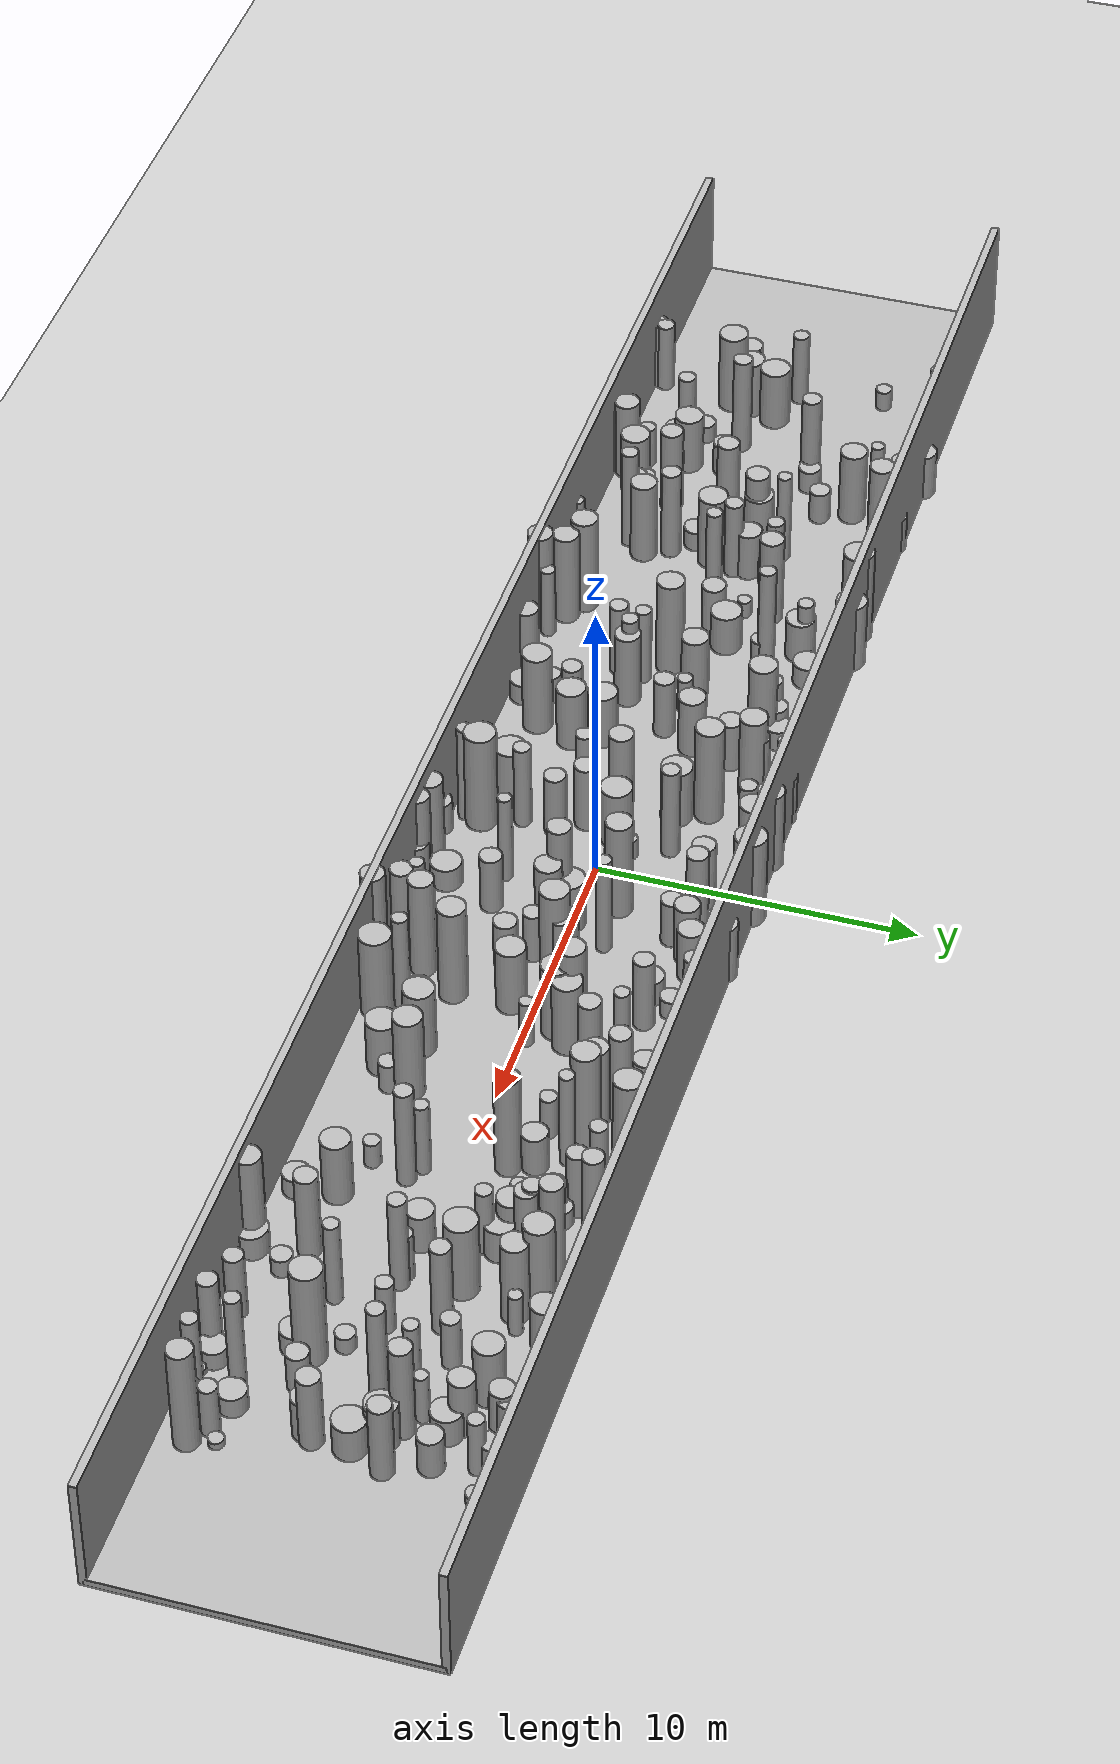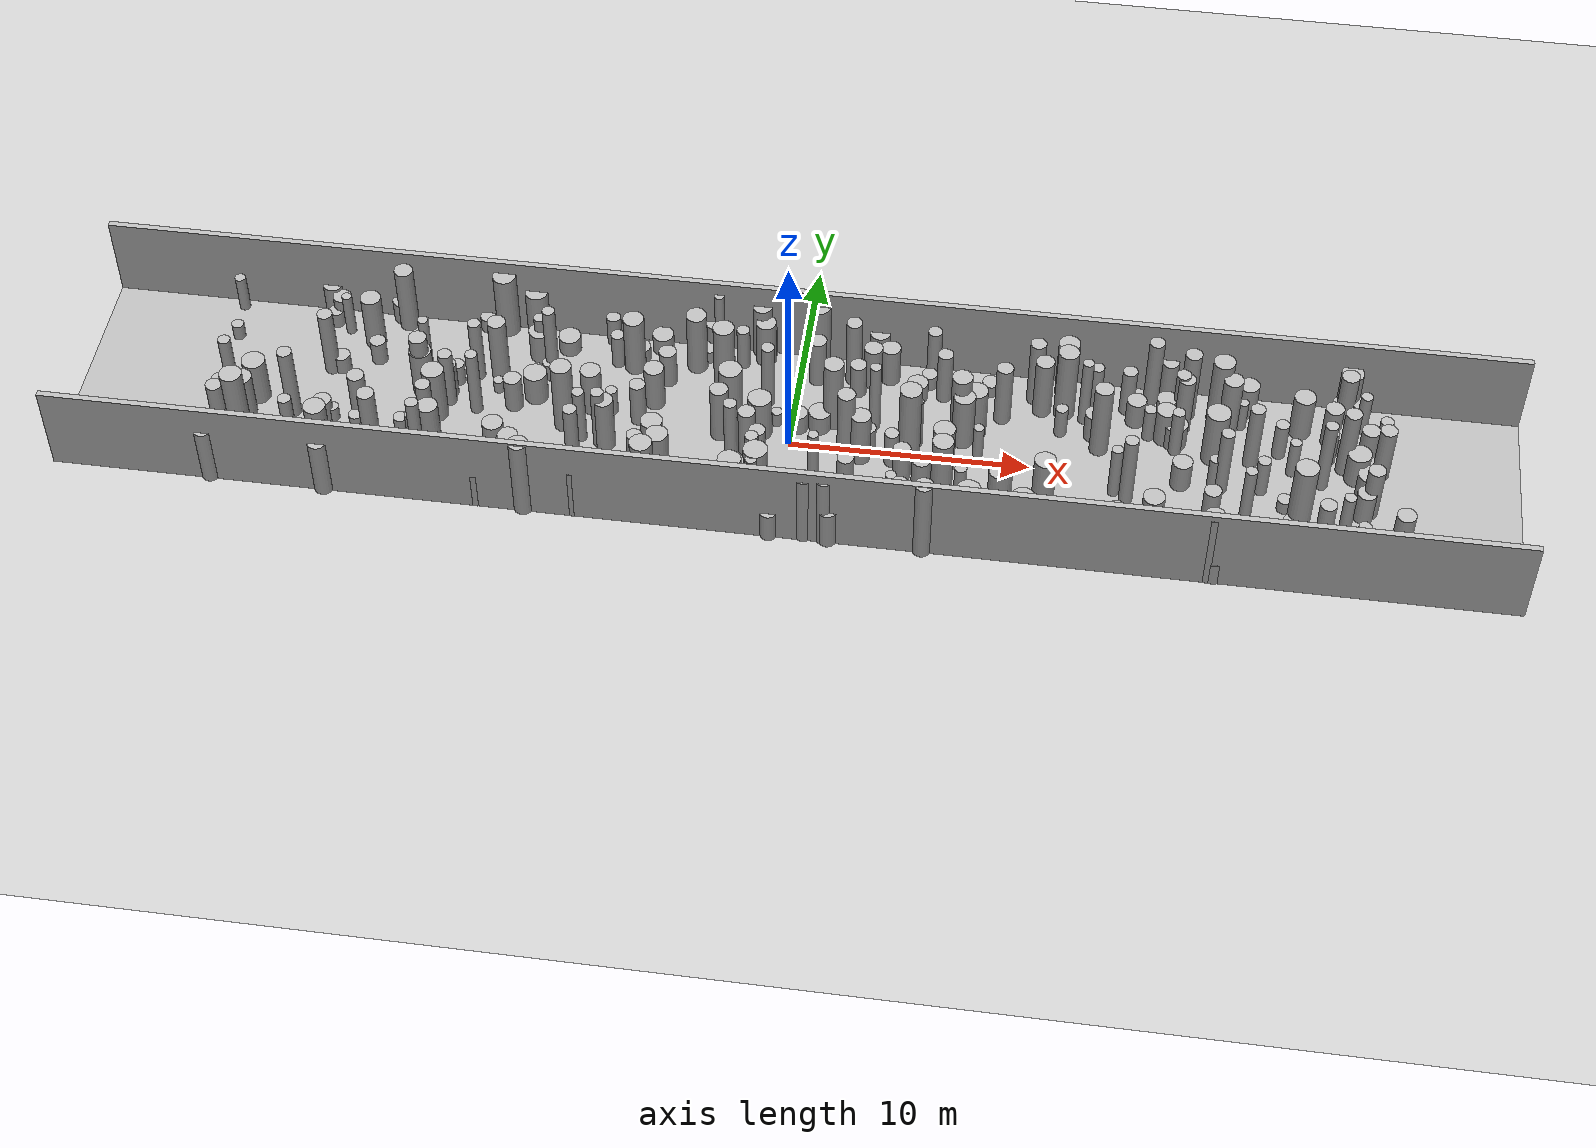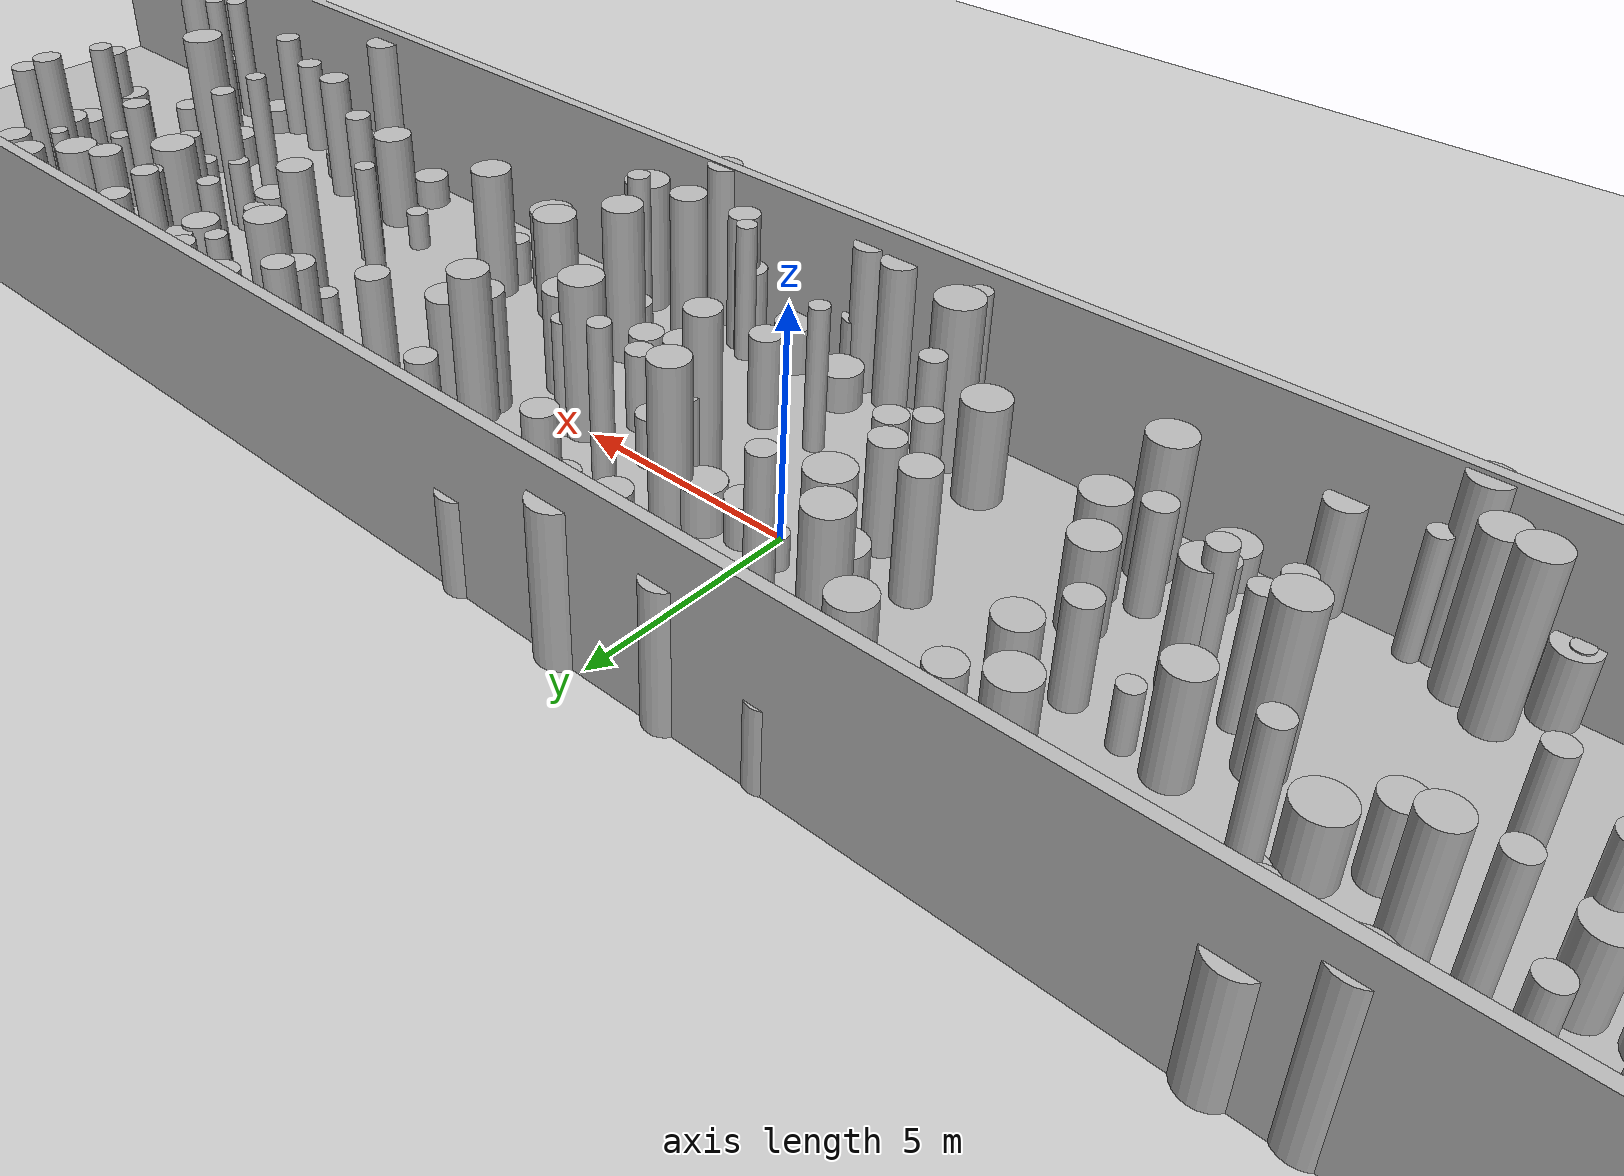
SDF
<?xml version="1.0"?>
<sdf version="1.4">
  <world name="default">
    <gui>
      <camera name="user_camera">
        <pose>-20 -30 40 0 0.66 0.83</pose>
      </camera>
    </gui>
    <include>
      <uri>model://ground_plane</uri>
    </include>
    <include>
      <uri>model://sun</uri>
    </include>
    <scene>
      <shadows>0</shadows>
    </scene>
    <model name="forest">
      <static>true</static>
      <link name="cylinder0">
        <pose>20.96834527113682 -1.8330656644667185 1.8838990508222753 0 0 0 </pose>
        <visual name="visual">
          <geometry>
            <cylinder>
              <radius>0.4776604967879795</radius>
              <length>3.7677981016445505</length>
            </cylinder>
          </geometry>
        </visual>
        <collision name="collision">
          <geometry>
            <cylinder>
              <radius>0.4776604967879795</radius>
              <length>3.7677981016445505</length>
            </cylinder>
          </geometry>
          <max_contacts>0</max_contacts>
        </collision>
      </link>
      <link name="cylinder1">
        <pose>3.2564242032673008 0.07752517679849902 0.6887090707186099 0 0 0 </pose>
        <visual name="visual">
          <geometry>
            <cylinder>
              <radius>0.3346961968090023</radius>
              <length>1.3774181414372197</length>
            </cylinder>
          </geometry>
        </visual>
        <collision name="collision">
          <geometry>
            <cylinder>
              <radius>0.3346961968090023</radius>
              <length>1.3774181414372197</length>
            </cylinder>
          </geometry>
          <max_contacts>0</max_contacts>
        </collision>
      </link>
      <link name="cylinder2">
        <pose>-14.566319184506593 0.7028453761987299 0.9826855995600178 0 0 0 </pose>
        <visual name="visual">
          <geometry>
            <cylinder>
              <radius>0.42092513275544663</radius>
              <length>1.9653711991200356</length>
            </cylinder>
          </geometry>
        </visual>
        <collision name="collision">
          <geometry>
            <cylinder>
              <radius>0.42092513275544663</radius>
              <length>1.9653711991200356</length>
            </cylinder>
          </geometry>
          <max_contacts>0</max_contacts>
        </collision>
      </link>
      <link name="cylinder3">
        <pose>-5.122488635472312 -2.3613867359242913 1.2156791975781638 0 0 0 </pose>
        <visual name="visual">
          <geometry>
            <cylinder>
              <radius>0.4657114707113331</radius>
              <length>2.4313583951563276</length>
            </cylinder>
          </geometry>
        </visual>
        <collision name="collision">
          <geometry>
            <cylinder>
              <radius>0.4657114707113331</radius>
              <length>2.4313583951563276</length>
            </cylinder>
          </geometry>
          <max_contacts>0</max_contacts>
        </collision>
      </link>
      <link name="cylinder4">
        <pose>23.599087777781456 -1.0351329412681909 0.8744894573423656 0 0 0 </pose>
        <visual name="visual">
          <geometry>
            <cylinder>
              <radius>0.396557973357214</radius>
              <length>1.7489789146847312</length>
            </cylinder>
          </geometry>
        </visual>
        <collision name="collision">
          <geometry>
            <cylinder>
              <radius>0.396557973357214</radius>
              <length>1.7489789146847312</length>
            </cylinder>
          </geometry>
          <max_contacts>0</max_contacts>
        </collision>
      </link>
      <link name="cylinder5">
        <pose>15.412757055949108 4.757021105903103 1.0764915467931095 0 0 0 </pose>
        <visual name="visual">
          <geometry>
            <cylinder>
              <radius>0.34895275617329075</radius>
              <length>2.152983093586219</length>
            </cylinder>
          </geometry>
        </visual>
        <collision name="collision">
          <geometry>
            <cylinder>
              <radius>0.34895275617329075</radius>
              <length>2.152983093586219</length>
            </cylinder>
          </geometry>
          <max_contacts>0</max_contacts>
        </collision>
      </link>
      <link name="cylinder6">
        <pose>15.371764462092166 2.155838014274546 1.015251472287274 0 0 0 </pose>
        <visual name="visual">
          <geometry>
            <cylinder>
              <radius>0.4205340897621195</radius>
              <length>2.030502944574548</length>
            </cylinder>
          </geometry>
        </visual>
        <collision name="collision">
          <geometry>
            <cylinder>
              <radius>0.4205340897621195</radius>
              <length>2.030502944574548</length>
            </cylinder>
          </geometry>
          <max_contacts>0</max_contacts>
        </collision>
      </link>
      <link name="cylinder7">
        <pose>-2.8999232739820577 -0.09374757711382031 1.506481006574513 0 0 0 </pose>
        <visual name="visual">
          <geometry>
            <cylinder>
              <radius>0.3824475917245142</radius>
              <length>3.012962013149026</length>
            </cylinder>
          </geometry>
        </visual>
        <collision name="collision">
          <geometry>
            <cylinder>
              <radius>0.3824475917245142</radius>
              <length>3.012962013149026</length>
            </cylinder>
          </geometry>
          <max_contacts>0</max_contacts>
        </collision>
      </link>
      <link name="cylinder8">
        <pose>-7.0236360223681125 3.224380381597209 1.5857802473510327 0 0 0 </pose>
        <visual name="visual">
          <geometry>
            <cylinder>
              <radius>0.4432136314929549</radius>
              <length>3.1715604947020655</length>
            </cylinder>
          </geometry>
        </visual>
        <collision name="collision">
          <geometry>
            <cylinder>
              <radius>0.4432136314929549</radius>
              <length>3.1715604947020655</length>
            </cylinder>
          </geometry>
          <max_contacts>0</max_contacts>
        </collision>
      </link>
      <link name="cylinder9">
        <pose>-1.802328232285305 4.905136888040609 1.4747844364075426 0 0 0 </pose>
        <visual name="visual">
          <geometry>
            <cylinder>
              <radius>0.4163657963996544</radius>
              <length>2.9495688728150853</length>
            </cylinder>
          </geometry>
        </visual>
        <collision name="collision">
          <geometry>
            <cylinder>
              <radius>0.4163657963996544</radius>
              <length>2.9495688728150853</length>
            </cylinder>
          </geometry>
          <max_contacts>0</max_contacts>
        </collision>
      </link>
      <link name="cylinder10">
        <pose>6.791761685345708 2.8088955088722827 1.023787186079001 0 0 0 </pose>
        <visual name="visual">
          <geometry>
            <cylinder>
              <radius>0.23918400872475332</radius>
              <length>2.047574372158002</length>
            </cylinder>
          </geometry>
        </visual>
        <collision name="collision">
          <geometry>
            <cylinder>
              <radius>0.23918400872475332</radius>
              <length>2.047574372158002</length>
            </cylinder>
          </geometry>
          <max_contacts>0</max_contacts>
        </collision>
      </link>
      <link name="cylinder11">
        <pose>10.651312184794094 -2.3999264610514115 1.6351353151789219 0 0 0 </pose>
        <visual name="visual">
          <geometry>
            <cylinder>
              <radius>0.44567808759371785</radius>
              <length>3.2702706303578437</length>
            </cylinder>
          </geometry>
        </visual>
        <collision name="collision">
          <geometry>
            <cylinder>
              <radius>0.44567808759371785</radius>
              <length>3.2702706303578437</length>
            </cylinder>
          </geometry>
          <max_contacts>0</max_contacts>
        </collision>
      </link>
      <link name="cylinder12">
        <pose>14.140751424714203 2.9823537584373385 0.7765425802694257 0 0 0 </pose>
        <visual name="visual">
          <geometry>
            <cylinder>
              <radius>0.40542205674459664</radius>
              <length>1.5530851605388514</length>
            </cylinder>
          </geometry>
        </visual>
        <collision name="collision">
          <geometry>
            <cylinder>
              <radius>0.40542205674459664</radius>
              <length>1.5530851605388514</length>
            </cylinder>
          </geometry>
          <max_contacts>0</max_contacts>
        </collision>
      </link>
      <link name="cylinder13">
        <pose>21.859361293917495 -4.293344875597363 0.44309726379591274 0 0 0 </pose>
        <visual name="visual">
          <geometry>
            <cylinder>
              <radius>0.42186271372300277</radius>
              <length>0.8861945275918255</length>
            </cylinder>
          </geometry>
        </visual>
        <collision name="collision">
          <geometry>
            <cylinder>
              <radius>0.42186271372300277</radius>
              <length>0.8861945275918255</length>
            </cylinder>
          </geometry>
          <max_contacts>0</max_contacts>
        </collision>
      </link>
      <link name="cylinder14">
        <pose>-0.9298519685459574 -4.436935589565988 1.9091290417879494 0 0 0 </pose>
        <visual name="visual">
          <geometry>
            <cylinder>
              <radius>0.23941363625729387</radius>
              <length>3.818258083575899</length>
            </cylinder>
          </geometry>
        </visual>
        <collision name="collision">
          <geometry>
            <cylinder>
              <radius>0.23941363625729387</radius>
              <length>3.818258083575899</length>
            </cylinder>
          </geometry>
          <max_contacts>0</max_contacts>
        </collision>
      </link>
      <link name="cylinder15">
        <pose>6.104734048057843 3.266509318063447 1.4293813778876574 0 0 0 </pose>
        <visual name="visual">
          <geometry>
            <cylinder>
              <radius>0.32012026691112394</radius>
              <length>2.858762755775315</length>
            </cylinder>
          </geometry>
        </visual>
        <collision name="collision">
          <geometry>
            <cylinder>
              <radius>0.32012026691112394</radius>
              <length>2.858762755775315</length>
            </cylinder>
          </geometry>
          <max_contacts>0</max_contacts>
        </collision>
      </link>
      <link name="cylinder16">
        <pose>5.537779644955908 4.593302339712308 1.3898717767210509 0 0 0 </pose>
        <visual name="visual">
          <geometry>
            <cylinder>
              <radius>0.29707722237790335</radius>
              <length>2.7797435534421018</length>
            </cylinder>
          </geometry>
        </visual>
        <collision name="collision">
          <geometry>
            <cylinder>
              <radius>0.29707722237790335</radius>
              <length>2.7797435534421018</length>
            </cylinder>
          </geometry>
          <max_contacts>0</max_contacts>
        </collision>
      </link>
      <link name="cylinder17">
        <pose>-4.492476951617313 3.7887865394801725 1.2449095618742323 0 0 0 </pose>
        <visual name="visual">
          <geometry>
            <cylinder>
              <radius>0.34079880354094694</radius>
              <length>2.4898191237484646</length>
            </cylinder>
          </geometry>
        </visual>
        <collision name="collision">
          <geometry>
            <cylinder>
              <radius>0.34079880354094694</radius>
              <length>2.4898191237484646</length>
            </cylinder>
          </geometry>
          <max_contacts>0</max_contacts>
        </collision>
      </link>
      <link name="cylinder18">
        <pose>-10.430794908742518 2.4155092818971093 1.9922489770107052 0 0 0 </pose>
        <visual name="visual">
          <geometry>
            <cylinder>
              <radius>0.26564784858792667</radius>
              <length>3.9844979540214105</length>
            </cylinder>
          </geometry>
        </visual>
        <collision name="collision">
          <geometry>
            <cylinder>
              <radius>0.26564784858792667</radius>
              <length>3.9844979540214105</length>
            </cylinder>
          </geometry>
          <max_contacts>0</max_contacts>
        </collision>
      </link>
      <link name="cylinder19">
        <pose>16.078526141087224 2.83666877780985 1.623034743778622 0 0 0 </pose>
        <visual name="visual">
          <geometry>
            <cylinder>
              <radius>0.3476683043780082</radius>
              <length>3.246069487557244</length>
            </cylinder>
          </geometry>
        </visual>
        <collision name="collision">
          <geometry>
            <cylinder>
              <radius>0.3476683043780082</radius>
              <length>3.246069487557244</length>
            </cylinder>
          </geometry>
          <max_contacts>0</max_contacts>
        </collision>
      </link>
      <link name="cylinder20">
        <pose>23.361852879667993 4.180324200057687 0.7042002919071049 0 0 0 </pose>
        <visual name="visual">
          <geometry>
            <cylinder>
              <radius>0.37907809096489864</radius>
              <length>1.4084005838142097</length>
            </cylinder>
          </geometry>
        </visual>
        <collision name="collision">
          <geometry>
            <cylinder>
              <radius>0.37907809096489864</radius>
              <length>1.4084005838142097</length>
            </cylinder>
          </geometry>
          <max_contacts>0</max_contacts>
        </collision>
      </link>
      <link name="cylinder21">
        <pose>6.955385285126042 1.345967827157315 1.8070522659248547 0 0 0 </pose>
        <visual name="visual">
          <geometry>
            <cylinder>
              <radius>0.42112964293394906</radius>
              <length>3.6141045318497094</length>
            </cylinder>
          </geometry>
        </visual>
        <collision name="collision">
          <geometry>
            <cylinder>
              <radius>0.42112964293394906</radius>
              <length>3.6141045318497094</length>
            </cylinder>
          </geometry>
          <max_contacts>0</max_contacts>
        </collision>
      </link>
      <link name="cylinder22">
        <pose>6.044731473526809 -4.981266680851473 1.986304914909412 0 0 0 </pose>
        <visual name="visual">
          <geometry>
            <cylinder>
              <radius>0.3771859304635002</radius>
              <length>3.972609829818824</length>
            </cylinder>
          </geometry>
        </visual>
        <collision name="collision">
          <geometry>
            <cylinder>
              <radius>0.3771859304635002</radius>
              <length>3.972609829818824</length>
            </cylinder>
          </geometry>
          <max_contacts>0</max_contacts>
        </collision>
      </link>
      <link name="cylinder23">
        <pose>-11.113900278116361 3.506994385561457 1.1926996139202175 0 0 0 </pose>
        <visual name="visual">
          <geometry>
            <cylinder>
              <radius>0.25347930996211976</radius>
              <length>2.385399227840435</length>
            </cylinder>
          </geometry>
        </visual>
        <collision name="collision">
          <geometry>
            <cylinder>
              <radius>0.25347930996211976</radius>
              <length>2.385399227840435</length>
            </cylinder>
          </geometry>
          <max_contacts>0</max_contacts>
        </collision>
      </link>
      <link name="cylinder24">
        <pose>-12.494464114637355 1.1501678156684978 0.4267576999208971 0 0 0 </pose>
        <visual name="visual">
          <geometry>
            <cylinder>
              <radius>0.22525729497200683</radius>
              <length>0.8535153998417943</length>
            </cylinder>
          </geometry>
        </visual>
        <collision name="collision">
          <geometry>
            <cylinder>
              <radius>0.22525729497200683</radius>
              <length>0.8535153998417943</length>
            </cylinder>
          </geometry>
          <max_contacts>0</max_contacts>
        </collision>
      </link>
      <link name="cylinder25">
        <pose>-0.17187193934478628 -4.988892364082588 0.6999133182070076 0 0 0 </pose>
        <visual name="visual">
          <geometry>
            <cylinder>
              <radius>0.3573136815506278</radius>
              <length>1.3998266364140153</length>
            </cylinder>
          </geometry>
        </visual>
        <collision name="collision">
          <geometry>
            <cylinder>
              <radius>0.3573136815506278</radius>
              <length>1.3998266364140153</length>
            </cylinder>
          </geometry>
          <max_contacts>0</max_contacts>
        </collision>
      </link>
      <link name="cylinder26">
        <pose>24.665532515206635 -3.2151725143366505 0.24761049663770013 0 0 0 </pose>
        <visual name="visual">
          <geometry>
            <cylinder>
              <radius>0.2331962708873026</radius>
              <length>0.49522099327540026</length>
            </cylinder>
          </geometry>
        </visual>
        <collision name="collision">
          <geometry>
            <cylinder>
              <radius>0.2331962708873026</radius>
              <length>0.49522099327540026</length>
            </cylinder>
          </geometry>
          <max_contacts>0</max_contacts>
        </collision>
      </link>
      <link name="cylinder27">
        <pose>-3.634349828456262 4.81314828473171 1.6950890789939468 0 0 0 </pose>
        <visual name="visual">
          <geometry>
            <cylinder>
              <radius>0.2065707765437049</radius>
              <length>3.3901781579878936</length>
            </cylinder>
          </geometry>
        </visual>
        <collision name="collision">
          <geometry>
            <cylinder>
              <radius>0.2065707765437049</radius>
              <length>3.3901781579878936</length>
            </cylinder>
          </geometry>
          <max_contacts>0</max_contacts>
        </collision>
      </link>
      <link name="cylinder28">
        <pose>1.3085077485909977 -2.460347573580645 1.7272098805406635 0 0 0 </pose>
        <visual name="visual">
          <geometry>
            <cylinder>
              <radius>0.2170416878893495</radius>
              <length>3.454419761081327</length>
            </cylinder>
          </geometry>
        </visual>
        <collision name="collision">
          <geometry>
            <cylinder>
              <radius>0.2170416878893495</radius>
              <length>3.454419761081327</length>
            </cylinder>
          </geometry>
          <max_contacts>0</max_contacts>
        </collision>
      </link>
      <link name="cylinder29">
        <pose>2.404971013464589 -0.4310649447777912 1.9083270513550894 0 0 0 </pose>
        <visual name="visual">
          <geometry>
            <cylinder>
              <radius>0.37260937327539334</radius>
              <length>3.816654102710179</length>
            </cylinder>
          </geometry>
        </visual>
        <collision name="collision">
          <geometry>
            <cylinder>
              <radius>0.37260937327539334</radius>
              <length>3.816654102710179</length>
            </cylinder>
          </geometry>
          <max_contacts>0</max_contacts>
        </collision>
      </link>
      <link name="cylinder30">
        <pose>-9.961078980103949 3.9041506113809135 0.5276463428228065 0 0 0 </pose>
        <visual name="visual">
          <geometry>
            <cylinder>
              <radius>0.47039764107652066</radius>
              <length>1.055292685645613</length>
            </cylinder>
          </geometry>
        </visual>
        <collision name="collision">
          <geometry>
            <cylinder>
              <radius>0.47039764107652066</radius>
              <length>1.055292685645613</length>
            </cylinder>
          </geometry>
          <max_contacts>0</max_contacts>
        </collision>
      </link>
      <link name="cylinder31">
        <pose>0.728083989314456 3.54254486332143 1.3202315058720475 0 0 0 </pose>
        <visual name="visual">
          <geometry>
            <cylinder>
              <radius>0.3638279688099043</radius>
              <length>2.640463011744095</length>
            </cylinder>
          </geometry>
        </visual>
        <collision name="collision">
          <geometry>
            <cylinder>
              <radius>0.3638279688099043</radius>
              <length>2.640463011744095</length>
            </cylinder>
          </geometry>
          <max_contacts>0</max_contacts>
        </collision>
      </link>
      <link name="cylinder32">
        <pose>1.6788921358952607 1.1993942715457875 1.8939832569953592 0 0 0 </pose>
        <visual name="visual">
          <geometry>
            <cylinder>
              <radius>0.4148775585149604</radius>
              <length>3.7879665139907184</length>
            </cylinder>
          </geometry>
        </visual>
        <collision name="collision">
          <geometry>
            <cylinder>
              <radius>0.4148775585149604</radius>
              <length>3.7879665139907184</length>
            </cylinder>
          </geometry>
          <max_contacts>0</max_contacts>
        </collision>
      </link>
      <link name="cylinder33">
        <pose>-11.503773523743948 -3.86456465136495 1.8933477084865609 0 0 0 </pose>
        <visual name="visual">
          <geometry>
            <cylinder>
              <radius>0.4279755908942054</radius>
              <length>3.7866954169731217</length>
            </cylinder>
          </geometry>
        </visual>
        <collision name="collision">
          <geometry>
            <cylinder>
              <radius>0.4279755908942054</radius>
              <length>3.7866954169731217</length>
            </cylinder>
          </geometry>
          <max_contacts>0</max_contacts>
        </collision>
      </link>
      <link name="cylinder34">
        <pose>15.25792517012706 -4.229375189393558 0.4910643464159582 0 0 0 </pose>
        <visual name="visual">
          <geometry>
            <cylinder>
              <radius>0.41456057884511044</radius>
              <length>0.9821286928319164</length>
            </cylinder>
          </geometry>
        </visual>
        <collision name="collision">
          <geometry>
            <cylinder>
              <radius>0.41456057884511044</radius>
              <length>0.9821286928319164</length>
            </cylinder>
          </geometry>
          <max_contacts>0</max_contacts>
        </collision>
      </link>
      <link name="cylinder35">
        <pose>9.916403407554988 -3.455078577531471 1.0699396154413097 0 0 0 </pose>
        <visual name="visual">
          <geometry>
            <cylinder>
              <radius>0.4895244351235126</radius>
              <length>2.1398792308826193</length>
            </cylinder>
          </geometry>
        </visual>
        <collision name="collision">
          <geometry>
            <cylinder>
              <radius>0.4895244351235126</radius>
              <length>2.1398792308826193</length>
            </cylinder>
          </geometry>
          <max_contacts>0</max_contacts>
        </collision>
      </link>
      <link name="cylinder36">
        <pose>-6.6973774161171065 -4.380743526352093 0.5086563272206437 0 0 0 </pose>
        <visual name="visual">
          <geometry>
            <cylinder>
              <radius>0.46342555181468237</radius>
              <length>1.0173126544412874</length>
            </cylinder>
          </geometry>
        </visual>
        <collision name="collision">
          <geometry>
            <cylinder>
              <radius>0.46342555181468237</radius>
              <length>1.0173126544412874</length>
            </cylinder>
          </geometry>
          <max_contacts>0</max_contacts>
        </collision>
      </link>
      <link name="cylinder37">
        <pose>-14.919958367531716 -3.377166467839172 1.9728194324279933 0 0 0 </pose>
        <visual name="visual">
          <geometry>
            <cylinder>
              <radius>0.2671299328466602</radius>
              <length>3.9456388648559866</length>
            </cylinder>
          </geometry>
        </visual>
        <collision name="collision">
          <geometry>
            <cylinder>
              <radius>0.2671299328466602</radius>
              <length>3.9456388648559866</length>
            </cylinder>
          </geometry>
          <max_contacts>0</max_contacts>
        </collision>
      </link>
      <link name="cylinder38">
        <pose>2.26524067411021 3.833357288593625 1.1937416955672315 0 0 0 </pose>
        <visual name="visual">
          <geometry>
            <cylinder>
              <radius>0.2292795001273905</radius>
              <length>2.387483391134463</length>
            </cylinder>
          </geometry>
        </visual>
        <collision name="collision">
          <geometry>
            <cylinder>
              <radius>0.2292795001273905</radius>
              <length>2.387483391134463</length>
            </cylinder>
          </geometry>
          <max_contacts>0</max_contacts>
        </collision>
      </link>
      <link name="cylinder39">
        <pose>-2.7162705476524422 1.7193987070710506 1.1589220702754321 0 0 0 </pose>
        <visual name="visual">
          <geometry>
            <cylinder>
              <radius>0.49349913281860774</radius>
              <length>2.3178441405508643</length>
            </cylinder>
          </geometry>
        </visual>
        <collision name="collision">
          <geometry>
            <cylinder>
              <radius>0.49349913281860774</radius>
              <length>2.3178441405508643</length>
            </cylinder>
          </geometry>
          <max_contacts>0</max_contacts>
        </collision>
      </link>
      <link name="cylinder40">
        <pose>-19.003075502211548 -3.975678212042615 0.871332757629638 0 0 0 </pose>
        <visual name="visual">
          <geometry>
            <cylinder>
              <radius>0.2714177743334837</radius>
              <length>1.742665515259276</length>
            </cylinder>
          </geometry>
        </visual>
        <collision name="collision">
          <geometry>
            <cylinder>
              <radius>0.2714177743334837</radius>
              <length>1.742665515259276</length>
            </cylinder>
          </geometry>
          <max_contacts>0</max_contacts>
        </collision>
      </link>
      <link name="cylinder41">
        <pose>-5.509328714808603 2.6333064211266564 1.0193684135478573 0 0 0 </pose>
        <visual name="visual">
          <geometry>
            <cylinder>
              <radius>0.36856713328046853</radius>
              <length>2.0387368270957147</length>
            </cylinder>
          </geometry>
        </visual>
        <collision name="collision">
          <geometry>
            <cylinder>
              <radius>0.36856713328046853</radius>
              <length>2.0387368270957147</length>
            </cylinder>
          </geometry>
          <max_contacts>0</max_contacts>
        </collision>
      </link>
      <link name="cylinder42">
        <pose>22.515740052190843 4.260668662055249 0.6424772735031694 0 0 0 </pose>
        <visual name="visual">
          <geometry>
            <cylinder>
              <radius>0.3144780467212596</radius>
              <length>1.2849545470063388</length>
            </cylinder>
          </geometry>
        </visual>
        <collision name="collision">
          <geometry>
            <cylinder>
              <radius>0.3144780467212596</radius>
              <length>1.2849545470063388</length>
            </cylinder>
          </geometry>
          <max_contacts>0</max_contacts>
        </collision>
      </link>
      <link name="cylinder43">
        <pose>-14.471069798430447 -2.783552739605298 1.6023824915551828 0 0 0 </pose>
        <visual name="visual">
          <geometry>
            <cylinder>
              <radius>0.42628796045596007</radius>
              <length>3.2047649831103655</length>
            </cylinder>
          </geometry>
        </visual>
        <collision name="collision">
          <geometry>
            <cylinder>
              <radius>0.42628796045596007</radius>
              <length>3.2047649831103655</length>
            </cylinder>
          </geometry>
          <max_contacts>0</max_contacts>
        </collision>
      </link>
      <link name="cylinder44">
        <pose>3.0273326932905924 -0.5800720216594293 1.405011788090321 0 0 0 </pose>
        <visual name="visual">
          <geometry>
            <cylinder>
              <radius>0.415455200806534</radius>
              <length>2.810023576180642</length>
            </cylinder>
          </geometry>
        </visual>
        <collision name="collision">
          <geometry>
            <cylinder>
              <radius>0.415455200806534</radius>
              <length>2.810023576180642</length>
            </cylinder>
          </geometry>
          <max_contacts>0</max_contacts>
        </collision>
      </link>
      <link name="cylinder45">
        <pose>-15.134815938974638 -3.0454822984439778 1.0191008471254641 0 0 0 </pose>
        <visual name="visual">
          <geometry>
            <cylinder>
              <radius>0.47265679621448126</radius>
              <length>2.0382016942509282</length>
            </cylinder>
          </geometry>
        </visual>
        <collision name="collision">
          <geometry>
            <cylinder>
              <radius>0.47265679621448126</radius>
              <length>2.0382016942509282</length>
            </cylinder>
          </geometry>
          <max_contacts>0</max_contacts>
        </collision>
      </link>
      <link name="cylinder46">
        <pose>5.783984864103488 -3.5918344635417387 1.9369772607824403 0 0 0 </pose>
        <visual name="visual">
          <geometry>
            <cylinder>
              <radius>0.391452424119965</radius>
              <length>3.8739545215648805</length>
            </cylinder>
          </geometry>
        </visual>
        <collision name="collision">
          <geometry>
            <cylinder>
              <radius>0.391452424119965</radius>
              <length>3.8739545215648805</length>
            </cylinder>
          </geometry>
          <max_contacts>0</max_contacts>
        </collision>
      </link>
      <link name="cylinder47">
        <pose>20.960880622647927 3.29613990828315 1.1984671373985931 0 0 0 </pose>
        <visual name="visual">
          <geometry>
            <cylinder>
              <radius>0.45005492466763847</radius>
              <length>2.3969342747971862</length>
            </cylinder>
          </geometry>
        </visual>
        <collision name="collision">
          <geometry>
            <cylinder>
              <radius>0.45005492466763847</radius>
              <length>2.3969342747971862</length>
            </cylinder>
          </geometry>
          <max_contacts>0</max_contacts>
        </collision>
      </link>
      <link name="cylinder48">
        <pose>-17.614040983702385 -2.6518937314884603 1.025482181448625 0 0 0 </pose>
        <visual name="visual">
          <geometry>
            <cylinder>
              <radius>0.28169031691605056</radius>
              <length>2.05096436289725</length>
            </cylinder>
          </geometry>
        </visual>
        <collision name="collision">
          <geometry>
            <cylinder>
              <radius>0.28169031691605056</radius>
              <length>2.05096436289725</length>
            </cylinder>
          </geometry>
          <max_contacts>0</max_contacts>
        </collision>
      </link>
      <link name="cylinder49">
        <pose>7.8100908553485695 0.22763244544070194 0.9541941109467907 0 0 0 </pose>
        <visual name="visual">
          <geometry>
            <cylinder>
              <radius>0.21466843039778039</radius>
              <length>1.9083882218935815</length>
            </cylinder>
          </geometry>
        </visual>
        <collision name="collision">
          <geometry>
            <cylinder>
              <radius>0.21466843039778039</radius>
              <length>1.9083882218935815</length>
            </cylinder>
          </geometry>
          <max_contacts>0</max_contacts>
        </collision>
      </link>
      <link name="cylinder50">
        <pose>-23.339157137945804 -4.9439633344894816 1.3639078894915722 0 0 0 </pose>
        <visual name="visual">
          <geometry>
            <cylinder>
              <radius>0.37375193587891997</radius>
              <length>2.7278157789831443</length>
            </cylinder>
          </geometry>
        </visual>
        <collision name="collision">
          <geometry>
            <cylinder>
              <radius>0.37375193587891997</radius>
              <length>2.7278157789831443</length>
            </cylinder>
          </geometry>
          <max_contacts>0</max_contacts>
        </collision>
      </link>
      <link name="cylinder51">
        <pose>2.6313243981090366 -2.4872664898439076 1.1429433010443504 0 0 0 </pose>
        <visual name="visual">
          <geometry>
            <cylinder>
              <radius>0.34634073661418713</radius>
              <length>2.2858866020887008</length>
            </cylinder>
          </geometry>
        </visual>
        <collision name="collision">
          <geometry>
            <cylinder>
              <radius>0.34634073661418713</radius>
              <length>2.2858866020887008</length>
            </cylinder>
          </geometry>
          <max_contacts>0</max_contacts>
        </collision>
      </link>
      <link name="cylinder52">
        <pose>8.912833237657999 -2.6606538914656475 1.3317041731425412 0 0 0 </pose>
        <visual name="visual">
          <geometry>
            <cylinder>
              <radius>0.47816389933437026</radius>
              <length>2.6634083462850824</length>
            </cylinder>
          </geometry>
        </visual>
        <collision name="collision">
          <geometry>
            <cylinder>
              <radius>0.47816389933437026</radius>
              <length>2.6634083462850824</length>
            </cylinder>
          </geometry>
          <max_contacts>0</max_contacts>
        </collision>
      </link>
      <link name="cylinder53">
        <pose>-23.48289043818395 -1.7341038883323856 1.1600301535751878 0 0 0 </pose>
        <visual name="visual">
          <geometry>
            <cylinder>
              <radius>0.4289087387838289</radius>
              <length>2.3200603071503756</length>
            </cylinder>
          </geometry>
        </visual>
        <collision name="collision">
          <geometry>
            <cylinder>
              <radius>0.4289087387838289</radius>
              <length>2.3200603071503756</length>
            </cylinder>
          </geometry>
          <max_contacts>0</max_contacts>
        </collision>
      </link>
      <link name="cylinder54">
        <pose>24.812494946747982 -4.002325983138089 1.996545816668052 0 0 0 </pose>
        <visual name="visual">
          <geometry>
            <cylinder>
              <radius>0.3845929586289015</radius>
              <length>3.993091633336104</length>
            </cylinder>
          </geometry>
        </visual>
        <collision name="collision">
          <geometry>
            <cylinder>
              <radius>0.3845929586289015</radius>
              <length>3.993091633336104</length>
            </cylinder>
          </geometry>
          <max_contacts>0</max_contacts>
        </collision>
      </link>
      <link name="cylinder55">
        <pose>-19.306139237631708 1.4754266966918284 0.5423400526042698 0 0 0 </pose>
        <visual name="visual">
          <geometry>
            <cylinder>
              <radius>0.3595567008579257</radius>
              <length>1.0846801052085395</length>
            </cylinder>
          </geometry>
        </visual>
        <collision name="collision">
          <geometry>
            <cylinder>
              <radius>0.3595567008579257</radius>
              <length>1.0846801052085395</length>
            </cylinder>
          </geometry>
          <max_contacts>0</max_contacts>
        </collision>
      </link>
      <link name="cylinder56">
        <pose>-1.099160007991685 -1.6428546513628994 1.2392589163798748 0 0 0 </pose>
        <visual name="visual">
          <geometry>
            <cylinder>
              <radius>0.34151896409971805</radius>
              <length>2.4785178327597497</length>
            </cylinder>
          </geometry>
        </visual>
        <collision name="collision">
          <geometry>
            <cylinder>
              <radius>0.34151896409971805</radius>
              <length>2.4785178327597497</length>
            </cylinder>
          </geometry>
          <max_contacts>0</max_contacts>
        </collision>
      </link>
      <link name="cylinder57">
        <pose>20.671730951437397 0.9941188210773557 1.0494021777304767 0 0 0 </pose>
        <visual name="visual">
          <geometry>
            <cylinder>
              <radius>0.23454435223153525</radius>
              <length>2.0988043554609535</length>
            </cylinder>
          </geometry>
        </visual>
        <collision name="collision">
          <geometry>
            <cylinder>
              <radius>0.23454435223153525</radius>
              <length>2.0988043554609535</length>
            </cylinder>
          </geometry>
          <max_contacts>0</max_contacts>
        </collision>
      </link>
      <link name="cylinder58">
        <pose>-5.860930529794846 1.3039277972030057 1.1827003225075265 0 0 0 </pose>
        <visual name="visual">
          <geometry>
            <cylinder>
              <radius>0.427066298406256</radius>
              <length>2.365400645015053</length>
            </cylinder>
          </geometry>
        </visual>
        <collision name="collision">
          <geometry>
            <cylinder>
              <radius>0.427066298406256</radius>
              <length>2.365400645015053</length>
            </cylinder>
          </geometry>
          <max_contacts>0</max_contacts>
        </collision>
      </link>
      <link name="cylinder59">
        <pose>21.20969406814173 0.2955652560846689 0.5527866696691696 0 0 0 </pose>
        <visual name="visual">
          <geometry>
            <cylinder>
              <radius>0.3075421207363877</radius>
              <length>1.1055733393383391</length>
            </cylinder>
          </geometry>
        </visual>
        <collision name="collision">
          <geometry>
            <cylinder>
              <radius>0.3075421207363877</radius>
              <length>1.1055733393383391</length>
            </cylinder>
          </geometry>
          <max_contacts>0</max_contacts>
        </collision>
      </link>
      <link name="cylinder60">
        <pose>21.889226632330043 0.4522090713417013 1.940199115371747 0 0 0 </pose>
        <visual name="visual">
          <geometry>
            <cylinder>
              <radius>0.26662985341586276</radius>
              <length>3.880398230743494</length>
            </cylinder>
          </geometry>
        </visual>
        <collision name="collision">
          <geometry>
            <cylinder>
              <radius>0.26662985341586276</radius>
              <length>3.880398230743494</length>
            </cylinder>
          </geometry>
          <max_contacts>0</max_contacts>
        </collision>
      </link>
      <link name="cylinder61">
        <pose>4.32019239198987 -0.6622430054170048 1.0125005073656888 0 0 0 </pose>
        <visual name="visual">
          <geometry>
            <cylinder>
              <radius>0.29732309763795045</radius>
              <length>2.0250010147313775</length>
            </cylinder>
          </geometry>
        </visual>
        <collision name="collision">
          <geometry>
            <cylinder>
              <radius>0.29732309763795045</radius>
              <length>2.0250010147313775</length>
            </cylinder>
          </geometry>
          <max_contacts>0</max_contacts>
        </collision>
      </link>
      <link name="cylinder62">
        <pose>12.46113262598842 1.9278681381600107 0.820351386576603 0 0 0 </pose>
        <visual name="visual">
          <geometry>
            <cylinder>
              <radius>0.39917872835598245</radius>
              <length>1.640702773153206</length>
            </cylinder>
          </geometry>
        </visual>
        <collision name="collision">
          <geometry>
            <cylinder>
              <radius>0.39917872835598245</radius>
              <length>1.640702773153206</length>
            </cylinder>
          </geometry>
          <max_contacts>0</max_contacts>
        </collision>
      </link>
      <link name="cylinder63">
        <pose>-19.390649685770157 -1.443232406159173 0.7014354620296043 0 0 0 </pose>
        <visual name="visual">
          <geometry>
            <cylinder>
              <radius>0.37918107197054185</radius>
              <length>1.4028709240592085</length>
            </cylinder>
          </geometry>
        </visual>
        <collision name="collision">
          <geometry>
            <cylinder>
              <radius>0.37918107197054185</radius>
              <length>1.4028709240592085</length>
            </cylinder>
          </geometry>
          <max_contacts>0</max_contacts>
        </collision>
      </link>
      <link name="cylinder64">
        <pose>23.774416207898035 2.551776331821407 0.7928464510793298 0 0 0 </pose>
        <visual name="visual">
          <geometry>
            <cylinder>
              <radius>0.3785299469800004</radius>
              <length>1.5856929021586597</length>
            </cylinder>
          </geometry>
        </visual>
        <collision name="collision">
          <geometry>
            <cylinder>
              <radius>0.3785299469800004</radius>
              <length>1.5856929021586597</length>
            </cylinder>
          </geometry>
          <max_contacts>0</max_contacts>
        </collision>
      </link>
      <link name="cylinder65">
        <pose>22.21560902879758 1.7947395433089106 1.002087049920516 0 0 0 </pose>
        <visual name="visual">
          <geometry>
            <cylinder>
              <radius>0.2072965654626761</radius>
              <length>2.004174099841032</length>
            </cylinder>
          </geometry>
        </visual>
        <collision name="collision">
          <geometry>
            <cylinder>
              <radius>0.2072965654626761</radius>
              <length>2.004174099841032</length>
            </cylinder>
          </geometry>
          <max_contacts>0</max_contacts>
        </collision>
      </link>
      <link name="cylinder66">
        <pose>7.10603062882609 -3.294566665885311 0.4725335632491016 0 0 0 </pose>
        <visual name="visual">
          <geometry>
            <cylinder>
              <radius>0.37222967705433707</radius>
              <length>0.9450671264982032</length>
            </cylinder>
          </geometry>
        </visual>
        <collision name="collision">
          <geometry>
            <cylinder>
              <radius>0.37222967705433707</radius>
              <length>0.9450671264982032</length>
            </cylinder>
          </geometry>
          <max_contacts>0</max_contacts>
        </collision>
      </link>
      <link name="cylinder67">
        <pose>19.431124389994913 -0.17708890974431846 1.0504100621950725 0 0 0 </pose>
        <visual name="visual">
          <geometry>
            <cylinder>
              <radius>0.26788737825701747</radius>
              <length>2.100820124390145</length>
            </cylinder>
          </geometry>
        </visual>
        <collision name="collision">
          <geometry>
            <cylinder>
              <radius>0.26788737825701747</radius>
              <length>2.100820124390145</length>
            </cylinder>
          </geometry>
          <max_contacts>0</max_contacts>
        </collision>
      </link>
      <link name="cylinder68">
        <pose>-14.423027307600734 0.23832079863513655 1.5465362854627644 0 0 0 </pose>
        <visual name="visual">
          <geometry>
            <cylinder>
              <radius>0.2976358405482731</radius>
              <length>3.093072570925529</length>
            </cylinder>
          </geometry>
        </visual>
        <collision name="collision">
          <geometry>
            <cylinder>
              <radius>0.2976358405482731</radius>
              <length>3.093072570925529</length>
            </cylinder>
          </geometry>
          <max_contacts>0</max_contacts>
        </collision>
      </link>
      <link name="cylinder69">
        <pose>-20.165813965108065 4.0985370996202395 0.49663304973153194 0 0 0 </pose>
        <visual name="visual">
          <geometry>
            <cylinder>
              <radius>0.32675639379643207</radius>
              <length>0.9932660994630639</length>
            </cylinder>
          </geometry>
        </visual>
        <collision name="collision">
          <geometry>
            <cylinder>
              <radius>0.32675639379643207</radius>
              <length>0.9932660994630639</length>
            </cylinder>
          </geometry>
          <max_contacts>0</max_contacts>
        </collision>
      </link>
      <link name="cylinder70">
        <pose>-20.868031552643117 -2.533850455858669 0.44335175028623147 0 0 0 </pose>
        <visual name="visual">
          <geometry>
            <cylinder>
              <radius>0.35519821692867615</radius>
              <length>0.8867035005724629</length>
            </cylinder>
          </geometry>
        </visual>
        <collision name="collision">
          <geometry>
            <cylinder>
              <radius>0.35519821692867615</radius>
              <length>0.8867035005724629</length>
            </cylinder>
          </geometry>
          <max_contacts>0</max_contacts>
        </collision>
      </link>
      <link name="cylinder71">
        <pose>-20.391767346869727 -3.0314551996646575 1.4980999452841675 0 0 0 </pose>
        <visual name="visual">
          <geometry>
            <cylinder>
              <radius>0.2773907891345589</radius>
              <length>2.996199890568335</length>
            </cylinder>
          </geometry>
        </visual>
        <collision name="collision">
          <geometry>
            <cylinder>
              <radius>0.2773907891345589</radius>
              <length>2.996199890568335</length>
            </cylinder>
          </geometry>
          <max_contacts>0</max_contacts>
        </collision>
      </link>
      <link name="cylinder72">
        <pose>2.2266979092676387 -4.957844107981716 0.9079458496091706 0 0 0 </pose>
        <visual name="visual">
          <geometry>
            <cylinder>
              <radius>0.3955183002997471</radius>
              <length>1.8158916992183411</length>
            </cylinder>
          </geometry>
        </visual>
        <collision name="collision">
          <geometry>
            <cylinder>
              <radius>0.3955183002997471</radius>
              <length>1.8158916992183411</length>
            </cylinder>
          </geometry>
          <max_contacts>0</max_contacts>
        </collision>
      </link>
      <link name="cylinder73">
        <pose>-7.370926659879757 3.579654666507505 0.6430692436108179 0 0 0 </pose>
        <visual name="visual">
          <geometry>
            <cylinder>
              <radius>0.3636783163257552</radius>
              <length>1.2861384872216357</length>
            </cylinder>
          </geometry>
        </visual>
        <collision name="collision">
          <geometry>
            <cylinder>
              <radius>0.3636783163257552</radius>
              <length>1.2861384872216357</length>
            </cylinder>
          </geometry>
          <max_contacts>0</max_contacts>
        </collision>
      </link>
      <link name="cylinder74">
        <pose>5.444044591681436 3.897154498007392 0.4669259545018768 0 0 0 </pose>
        <visual name="visual">
          <geometry>
            <cylinder>
              <radius>0.3276150434940689</radius>
              <length>0.9338519090037536</length>
            </cylinder>
          </geometry>
        </visual>
        <collision name="collision">
          <geometry>
            <cylinder>
              <radius>0.3276150434940689</radius>
              <length>0.9338519090037536</length>
            </cylinder>
          </geometry>
          <max_contacts>0</max_contacts>
        </collision>
      </link>
      <link name="cylinder75">
        <pose>-3.991210494456805 4.2090284095127615 0.4389880203142682 0 0 0 </pose>
        <visual name="visual">
          <geometry>
            <cylinder>
              <radius>0.3487157258938671</radius>
              <length>0.8779760406285364</length>
            </cylinder>
          </geometry>
        </visual>
        <collision name="collision">
          <geometry>
            <cylinder>
              <radius>0.3487157258938671</radius>
              <length>0.8779760406285364</length>
            </cylinder>
          </geometry>
          <max_contacts>0</max_contacts>
        </collision>
      </link>
      <link name="cylinder76">
        <pose>-0.8300043536209891 -3.911309800937982 1.925598462031068 0 0 0 </pose>
        <visual name="visual">
          <geometry>
            <cylinder>
              <radius>0.49771133099787124</radius>
              <length>3.851196924062136</length>
            </cylinder>
          </geometry>
        </visual>
        <collision name="collision">
          <geometry>
            <cylinder>
              <radius>0.49771133099787124</radius>
              <length>3.851196924062136</length>
            </cylinder>
          </geometry>
          <max_contacts>0</max_contacts>
        </collision>
      </link>
      <link name="cylinder77">
        <pose>-19.963547473010497 4.448358914176726 0.767138783690235 0 0 0 </pose>
        <visual name="visual">
          <geometry>
            <cylinder>
              <radius>0.39100425804760275</radius>
              <length>1.53427756738047</length>
            </cylinder>
          </geometry>
        </visual>
        <collision name="collision">
          <geometry>
            <cylinder>
              <radius>0.39100425804760275</radius>
              <length>1.53427756738047</length>
            </cylinder>
          </geometry>
          <max_contacts>0</max_contacts>
        </collision>
      </link>
      <link name="cylinder78">
        <pose>-13.20160754078895 -0.0830493010089377 1.7875002070733899 0 0 0 </pose>
        <visual name="visual">
          <geometry>
            <cylinder>
              <radius>0.2561081950243054</radius>
              <length>3.5750004141467797</length>
            </cylinder>
          </geometry>
        </visual>
        <collision name="collision">
          <geometry>
            <cylinder>
              <radius>0.2561081950243054</radius>
              <length>3.5750004141467797</length>
            </cylinder>
          </geometry>
          <max_contacts>0</max_contacts>
        </collision>
      </link>
      <link name="cylinder79">
        <pose>-8.78022704950251 -1.9174426073536264 1.4422593523172762 0 0 0 </pose>
        <visual name="visual">
          <geometry>
            <cylinder>
              <radius>0.29280142427542655</radius>
              <length>2.8845187046345524</length>
            </cylinder>
          </geometry>
        </visual>
        <collision name="collision">
          <geometry>
            <cylinder>
              <radius>0.29280142427542655</radius>
              <length>2.8845187046345524</length>
            </cylinder>
          </geometry>
          <max_contacts>0</max_contacts>
        </collision>
      </link>
      <link name="cylinder80">
        <pose>-15.057319476177494 -3.1597643583015 1.50444465342989 0 0 0 </pose>
        <visual name="visual">
          <geometry>
            <cylinder>
              <radius>0.2894952948640372</radius>
              <length>3.00888930685978</length>
            </cylinder>
          </geometry>
        </visual>
        <collision name="collision">
          <geometry>
            <cylinder>
              <radius>0.2894952948640372</radius>
              <length>3.00888930685978</length>
            </cylinder>
          </geometry>
          <max_contacts>0</max_contacts>
        </collision>
      </link>
      <link name="cylinder81">
        <pose>20.11186959243407 1.938806779890843 1.0360317320758266 0 0 0 </pose>
        <visual name="visual">
          <geometry>
            <cylinder>
              <radius>0.28269669089537774</radius>
              <length>2.072063464151653</length>
            </cylinder>
          </geometry>
        </visual>
        <collision name="collision">
          <geometry>
            <cylinder>
              <radius>0.28269669089537774</radius>
              <length>2.072063464151653</length>
            </cylinder>
          </geometry>
          <max_contacts>0</max_contacts>
        </collision>
      </link>
      <link name="cylinder82">
        <pose>24.25918216605914 -3.5209876316447875 1.0263778069098144 0 0 0 </pose>
        <visual name="visual">
          <geometry>
            <cylinder>
              <radius>0.27609513909367595</radius>
              <length>2.052755613819629</length>
            </cylinder>
          </geometry>
        </visual>
        <collision name="collision">
          <geometry>
            <cylinder>
              <radius>0.27609513909367595</radius>
              <length>2.052755613819629</length>
            </cylinder>
          </geometry>
          <max_contacts>0</max_contacts>
        </collision>
      </link>
      <link name="cylinder83">
        <pose>18.966907809114694 1.3075050766581233 1.7557089396479162 0 0 0 </pose>
        <visual name="visual">
          <geometry>
            <cylinder>
              <radius>0.30451281037348954</radius>
              <length>3.5114178792958324</length>
            </cylinder>
          </geometry>
        </visual>
        <collision name="collision">
          <geometry>
            <cylinder>
              <radius>0.30451281037348954</radius>
              <length>3.5114178792958324</length>
            </cylinder>
          </geometry>
          <max_contacts>0</max_contacts>
        </collision>
      </link>
      <link name="cylinder84">
        <pose>-7.510002033769503 -1.2627982842625673 1.4591379763917094 0 0 0 </pose>
        <visual name="visual">
          <geometry>
            <cylinder>
              <radius>0.40943335809178305</radius>
              <length>2.918275952783419</length>
            </cylinder>
          </geometry>
        </visual>
        <collision name="collision">
          <geometry>
            <cylinder>
              <radius>0.40943335809178305</radius>
              <length>2.918275952783419</length>
            </cylinder>
          </geometry>
          <max_contacts>0</max_contacts>
        </collision>
      </link>
      <link name="cylinder85">
        <pose>-22.428810283844424 -0.5667853174805417 1.202391158538445 0 0 0 </pose>
        <visual name="visual">
          <geometry>
            <cylinder>
              <radius>0.4937334557329827</radius>
              <length>2.40478231707689</length>
            </cylinder>
          </geometry>
        </visual>
        <collision name="collision">
          <geometry>
            <cylinder>
              <radius>0.4937334557329827</radius>
              <length>2.40478231707689</length>
            </cylinder>
          </geometry>
          <max_contacts>0</max_contacts>
        </collision>
      </link>
      <link name="cylinder86">
        <pose>6.5360003193010066 -2.4213013501345726 1.8937233072710862 0 0 0 </pose>
        <visual name="visual">
          <geometry>
            <cylinder>
              <radius>0.43426102784554876</radius>
              <length>3.7874466145421724</length>
            </cylinder>
          </geometry>
        </visual>
        <collision name="collision">
          <geometry>
            <cylinder>
              <radius>0.43426102784554876</radius>
              <length>3.7874466145421724</length>
            </cylinder>
          </geometry>
          <max_contacts>0</max_contacts>
        </collision>
      </link>
      <link name="cylinder87">
        <pose>2.224524331369583 3.7613691120727317 1.839508305520297 0 0 0 </pose>
        <visual name="visual">
          <geometry>
            <cylinder>
              <radius>0.3326603079593494</radius>
              <length>3.679016611040594</length>
            </cylinder>
          </geometry>
        </visual>
        <collision name="collision">
          <geometry>
            <cylinder>
              <radius>0.3326603079593494</radius>
              <length>3.679016611040594</length>
            </cylinder>
          </geometry>
          <max_contacts>0</max_contacts>
        </collision>
      </link>
      <link name="cylinder88">
        <pose>13.48762850743605 -1.070798751830584 1.4360413168927246 0 0 0 </pose>
        <visual name="visual">
          <geometry>
            <cylinder>
              <radius>0.23440285257273424</radius>
              <length>2.8720826337854493</length>
            </cylinder>
          </geometry>
        </visual>
        <collision name="collision">
          <geometry>
            <cylinder>
              <radius>0.23440285257273424</radius>
              <length>2.8720826337854493</length>
            </cylinder>
          </geometry>
          <max_contacts>0</max_contacts>
        </collision>
      </link>
      <link name="cylinder89">
        <pose>-11.113264922677535 3.3518798816660773 0.8726313053198396 0 0 0 </pose>
        <visual name="visual">
          <geometry>
            <cylinder>
              <radius>0.4664649839996773</radius>
              <length>1.7452626106396791</length>
            </cylinder>
          </geometry>
        </visual>
        <collision name="collision">
          <geometry>
            <cylinder>
              <radius>0.4664649839996773</radius>
              <length>1.7452626106396791</length>
            </cylinder>
          </geometry>
          <max_contacts>0</max_contacts>
        </collision>
      </link>
      <link name="cylinder90">
        <pose>14.73301092875409 4.338262694742593 1.8378489770257938 0 0 0 </pose>
        <visual name="visual">
          <geometry>
            <cylinder>
              <radius>0.3204598900029928</radius>
              <length>3.6756979540515875</length>
            </cylinder>
          </geometry>
        </visual>
        <collision name="collision">
          <geometry>
            <cylinder>
              <radius>0.3204598900029928</radius>
              <length>3.6756979540515875</length>
            </cylinder>
          </geometry>
          <max_contacts>0</max_contacts>
        </collision>
      </link>
      <link name="cylinder91">
        <pose>-10.250745611023454 -4.932685812237344 1.9586394836863317 0 0 0 </pose>
        <visual name="visual">
          <geometry>
            <cylinder>
              <radius>0.4076547631145858</radius>
              <length>3.9172789673726633</length>
            </cylinder>
          </geometry>
        </visual>
        <collision name="collision">
          <geometry>
            <cylinder>
              <radius>0.4076547631145858</radius>
              <length>3.9172789673726633</length>
            </cylinder>
          </geometry>
          <max_contacts>0</max_contacts>
        </collision>
      </link>
      <link name="cylinder92">
        <pose>-12.578372749424133 1.9805506755536149 1.739251106344664 0 0 0 </pose>
        <visual name="visual">
          <geometry>
            <cylinder>
              <radius>0.3822702057000762</radius>
              <length>3.478502212689328</length>
            </cylinder>
          </geometry>
        </visual>
        <collision name="collision">
          <geometry>
            <cylinder>
              <radius>0.3822702057000762</radius>
              <length>3.478502212689328</length>
            </cylinder>
          </geometry>
          <max_contacts>0</max_contacts>
        </collision>
      </link>
      <link name="cylinder93">
        <pose>12.421595035052121 3.800808972736476 1.2049492962238006 0 0 0 </pose>
        <visual name="visual">
          <geometry>
            <cylinder>
              <radius>0.26336484966202345</radius>
              <length>2.4098985924476013</length>
            </cylinder>
          </geometry>
        </visual>
        <collision name="collision">
          <geometry>
            <cylinder>
              <radius>0.26336484966202345</radius>
              <length>2.4098985924476013</length>
            </cylinder>
          </geometry>
          <max_contacts>0</max_contacts>
        </collision>
      </link>
      <link name="cylinder94">
        <pose>2.0167772814082454 -4.101800145312881 0.5404346776892284 0 0 0 </pose>
        <visual name="visual">
          <geometry>
            <cylinder>
              <radius>0.4892853747842669</radius>
              <length>1.0808693553784567</length>
            </cylinder>
          </geometry>
        </visual>
        <collision name="collision">
          <geometry>
            <cylinder>
              <radius>0.4892853747842669</radius>
              <length>1.0808693553784567</length>
            </cylinder>
          </geometry>
          <max_contacts>0</max_contacts>
        </collision>
      </link>
      <link name="cylinder95">
        <pose>-17.976783387011825 -0.9387285256849065 1.2737165180536838 0 0 0 </pose>
        <visual name="visual">
          <geometry>
            <cylinder>
              <radius>0.3621169185394072</radius>
              <length>2.5474330361073676</length>
            </cylinder>
          </geometry>
        </visual>
        <collision name="collision">
          <geometry>
            <cylinder>
              <radius>0.3621169185394072</radius>
              <length>2.5474330361073676</length>
            </cylinder>
          </geometry>
          <max_contacts>0</max_contacts>
        </collision>
      </link>
      <link name="cylinder96">
        <pose>8.032357894291543 3.8770866249073848 0.41748185190403564 0 0 0 </pose>
        <visual name="visual">
          <geometry>
            <cylinder>
              <radius>0.3667689242908239</radius>
              <length>0.8349637038080713</length>
            </cylinder>
          </geometry>
        </visual>
        <collision name="collision">
          <geometry>
            <cylinder>
              <radius>0.3667689242908239</radius>
              <length>0.8349637038080713</length>
            </cylinder>
          </geometry>
          <max_contacts>0</max_contacts>
        </collision>
      </link>
      <link name="cylinder97">
        <pose>-19.025995021560266 -1.3533691423489569 0.4696846900667888 0 0 0 </pose>
        <visual name="visual">
          <geometry>
            <cylinder>
              <radius>0.25177067801897535</radius>
              <length>0.9393693801335776</length>
            </cylinder>
          </geometry>
        </visual>
        <collision name="collision">
          <geometry>
            <cylinder>
              <radius>0.25177067801897535</radius>
              <length>0.9393693801335776</length>
            </cylinder>
          </geometry>
          <max_contacts>0</max_contacts>
        </collision>
      </link>
      <link name="cylinder98">
        <pose>0.2851709550141237 0.703721933528235 0.5992735812576785 0 0 0 </pose>
        <visual name="visual">
          <geometry>
            <cylinder>
              <radius>0.3905447183202788</radius>
              <length>1.198547162515357</length>
            </cylinder>
          </geometry>
        </visual>
        <collision name="collision">
          <geometry>
            <cylinder>
              <radius>0.3905447183202788</radius>
              <length>1.198547162515357</length>
            </cylinder>
          </geometry>
          <max_contacts>0</max_contacts>
        </collision>
      </link>
      <link name="cylinder99">
        <pose>23.83647285938465 -0.8034661330526696 1.447871330089927 0 0 0 </pose>
        <visual name="visual">
          <geometry>
            <cylinder>
              <radius>0.3496557820190463</radius>
              <length>2.895742660179854</length>
            </cylinder>
          </geometry>
        </visual>
        <collision name="collision">
          <geometry>
            <cylinder>
              <radius>0.3496557820190463</radius>
              <length>2.895742660179854</length>
            </cylinder>
          </geometry>
          <max_contacts>0</max_contacts>
        </collision>
      </link>
      <link name="cylinder100">
        <pose>-5.500254357732036 -1.4543770781961705 1.0914578403572304 0 0 0 </pose>
        <visual name="visual">
          <geometry>
            <cylinder>
              <radius>0.45783312673172627</radius>
              <length>2.1829156807144607</length>
            </cylinder>
          </geometry>
        </visual>
        <collision name="collision">
          <geometry>
            <cylinder>
              <radius>0.45783312673172627</radius>
              <length>2.1829156807144607</length>
            </cylinder>
          </geometry>
          <max_contacts>0</max_contacts>
        </collision>
      </link>
      <link name="cylinder101">
        <pose>-4.422683067388011 3.6356610109516136 1.6719912325273039 0 0 0 </pose>
        <visual name="visual">
          <geometry>
            <cylinder>
              <radius>0.42933856574625584</radius>
              <length>3.3439824650546077</length>
            </cylinder>
          </geometry>
        </visual>
        <collision name="collision">
          <geometry>
            <cylinder>
              <radius>0.42933856574625584</radius>
              <length>3.3439824650546077</length>
            </cylinder>
          </geometry>
          <max_contacts>0</max_contacts>
        </collision>
      </link>
      <link name="cylinder102">
        <pose>18.524006024574234 3.2665160891847496 0.8670781150907563 0 0 0 </pose>
        <visual name="visual">
          <geometry>
            <cylinder>
              <radius>0.20576172495890896</radius>
              <length>1.7341562301815125</length>
            </cylinder>
          </geometry>
        </visual>
        <collision name="collision">
          <geometry>
            <cylinder>
              <radius>0.20576172495890896</radius>
              <length>1.7341562301815125</length>
            </cylinder>
          </geometry>
          <max_contacts>0</max_contacts>
        </collision>
      </link>
      <link name="cylinder103">
        <pose>-2.5066376242943207 4.016763955130241 1.1631307201525414 0 0 0 </pose>
        <visual name="visual">
          <geometry>
            <cylinder>
              <radius>0.27461047342937306</radius>
              <length>2.3262614403050828</length>
            </cylinder>
          </geometry>
        </visual>
        <collision name="collision">
          <geometry>
            <cylinder>
              <radius>0.27461047342937306</radius>
              <length>2.3262614403050828</length>
            </cylinder>
          </geometry>
          <max_contacts>0</max_contacts>
        </collision>
      </link>
      <link name="cylinder104">
        <pose>13.65276268194917 -2.512169493709587 0.5801237906408758 0 0 0 </pose>
        <visual name="visual">
          <geometry>
            <cylinder>
              <radius>0.24784293589118667</radius>
              <length>1.1602475812817516</length>
            </cylinder>
          </geometry>
        </visual>
        <collision name="collision">
          <geometry>
            <cylinder>
              <radius>0.24784293589118667</radius>
              <length>1.1602475812817516</length>
            </cylinder>
          </geometry>
          <max_contacts>0</max_contacts>
        </collision>
      </link>
      <link name="cylinder105">
        <pose>20.087673183752244 -4.272707932242906 1.2937616115200432 0 0 0 </pose>
        <visual name="visual">
          <geometry>
            <cylinder>
              <radius>0.30029825554276496</radius>
              <length>2.5875232230400864</length>
            </cylinder>
          </geometry>
        </visual>
        <collision name="collision">
          <geometry>
            <cylinder>
              <radius>0.30029825554276496</radius>
              <length>2.5875232230400864</length>
            </cylinder>
          </geometry>
          <max_contacts>0</max_contacts>
        </collision>
      </link>
      <link name="cylinder106">
        <pose>20.790579526300093 -2.3107116602553113 0.515968621931586 0 0 0 </pose>
        <visual name="visual">
          <geometry>
            <cylinder>
              <radius>0.4522052166479336</radius>
              <length>1.031937243863172</length>
            </cylinder>
          </geometry>
        </visual>
        <collision name="collision">
          <geometry>
            <cylinder>
              <radius>0.4522052166479336</radius>
              <length>1.031937243863172</length>
            </cylinder>
          </geometry>
          <max_contacts>0</max_contacts>
        </collision>
      </link>
      <link name="cylinder107">
        <pose>5.241051815893687 0.4731844641226157 1.4195543714200514 0 0 0 </pose>
        <visual name="visual">
          <geometry>
            <cylinder>
              <radius>0.24144562408811893</radius>
              <length>2.8391087428401027</length>
            </cylinder>
          </geometry>
        </visual>
        <collision name="collision">
          <geometry>
            <cylinder>
              <radius>0.24144562408811893</radius>
              <length>2.8391087428401027</length>
            </cylinder>
          </geometry>
          <max_contacts>0</max_contacts>
        </collision>
      </link>
      <link name="cylinder108">
        <pose>-18.268168410941616 3.171330956501059 1.4633586836667556 0 0 0 </pose>
        <visual name="visual">
          <geometry>
            <cylinder>
              <radius>0.43181546055714903</radius>
              <length>2.926717367333511</length>
            </cylinder>
          </geometry>
        </visual>
        <collision name="collision">
          <geometry>
            <cylinder>
              <radius>0.43181546055714903</radius>
              <length>2.926717367333511</length>
            </cylinder>
          </geometry>
          <max_contacts>0</max_contacts>
        </collision>
      </link>
      <link name="cylinder109">
        <pose>16.236907004914627 3.615181665917685 1.966793187870496 0 0 0 </pose>
        <visual name="visual">
          <geometry>
            <cylinder>
              <radius>0.3476543113434448</radius>
              <length>3.933586375740992</length>
            </cylinder>
          </geometry>
        </visual>
        <collision name="collision">
          <geometry>
            <cylinder>
              <radius>0.3476543113434448</radius>
              <length>3.933586375740992</length>
            </cylinder>
          </geometry>
          <max_contacts>0</max_contacts>
        </collision>
      </link>
      <link name="cylinder110">
        <pose>21.36453451581584 -4.539301355390689 1.4452873677912157 0 0 0 </pose>
        <visual name="visual">
          <geometry>
            <cylinder>
              <radius>0.3044548254093685</radius>
              <length>2.8905747355824314</length>
            </cylinder>
          </geometry>
        </visual>
        <collision name="collision">
          <geometry>
            <cylinder>
              <radius>0.3044548254093685</radius>
              <length>2.8905747355824314</length>
            </cylinder>
          </geometry>
          <max_contacts>0</max_contacts>
        </collision>
      </link>
      <link name="cylinder111">
        <pose>-23.574563466632707 -2.379174157336098 1.3429333947595075 0 0 0 </pose>
        <visual name="visual">
          <geometry>
            <cylinder>
              <radius>0.34812483642246767</radius>
              <length>2.685866789519015</length>
            </cylinder>
          </geometry>
        </visual>
        <collision name="collision">
          <geometry>
            <cylinder>
              <radius>0.34812483642246767</radius>
              <length>2.685866789519015</length>
            </cylinder>
          </geometry>
          <max_contacts>0</max_contacts>
        </collision>
      </link>
      <link name="cylinder112">
        <pose>12.734495251852628 1.217216102082899 1.9496966208242075 0 0 0 </pose>
        <visual name="visual">
          <geometry>
            <cylinder>
              <radius>0.38599762271795157</radius>
              <length>3.899393241648415</length>
            </cylinder>
          </geometry>
        </visual>
        <collision name="collision">
          <geometry>
            <cylinder>
              <radius>0.38599762271795157</radius>
              <length>3.899393241648415</length>
            </cylinder>
          </geometry>
          <max_contacts>0</max_contacts>
        </collision>
      </link>
      <link name="cylinder113">
        <pose>7.116439502174096 0.9202964245391847 1.4633764514039878 0 0 0 </pose>
        <visual name="visual">
          <geometry>
            <cylinder>
              <radius>0.45558578414656775</radius>
              <length>2.9267529028079755</length>
            </cylinder>
          </geometry>
        </visual>
        <collision name="collision">
          <geometry>
            <cylinder>
              <radius>0.45558578414656775</radius>
              <length>2.9267529028079755</length>
            </cylinder>
          </geometry>
          <max_contacts>0</max_contacts>
        </collision>
      </link>
      <link name="cylinder114">
        <pose>22.561821439815162 2.6065542125423775 0.6233286959056551 0 0 0 </pose>
        <visual name="visual">
          <geometry>
            <cylinder>
              <radius>0.4658265185807811</radius>
              <length>1.2466573918113102</length>
            </cylinder>
          </geometry>
        </visual>
        <collision name="collision">
          <geometry>
            <cylinder>
              <radius>0.4658265185807811</radius>
              <length>1.2466573918113102</length>
            </cylinder>
          </geometry>
          <max_contacts>0</max_contacts>
        </collision>
      </link>
      <link name="cylinder115">
        <pose>6.459470260558199 -0.6646382515900031 1.3026173803792296 0 0 0 </pose>
        <visual name="visual">
          <geometry>
            <cylinder>
              <radius>0.4611315553172426</radius>
              <length>2.605234760758459</length>
            </cylinder>
          </geometry>
        </visual>
        <collision name="collision">
          <geometry>
            <cylinder>
              <radius>0.4611315553172426</radius>
              <length>2.605234760758459</length>
            </cylinder>
          </geometry>
          <max_contacts>0</max_contacts>
        </collision>
      </link>
      <link name="cylinder116">
        <pose>24.564871127579863 4.053175347701522 0.3115307732861888 0 0 0 </pose>
        <visual name="visual">
          <geometry>
            <cylinder>
              <radius>0.28134973749634645</radius>
              <length>0.6230615465723776</length>
            </cylinder>
          </geometry>
        </visual>
        <collision name="collision">
          <geometry>
            <cylinder>
              <radius>0.28134973749634645</radius>
              <length>0.6230615465723776</length>
            </cylinder>
          </geometry>
          <max_contacts>0</max_contacts>
        </collision>
      </link>
      <link name="cylinder117">
        <pose>-12.210336348332284 -4.729263539588812 0.871427749418527 0 0 0 </pose>
        <visual name="visual">
          <geometry>
            <cylinder>
              <radius>0.41497765760517946</radius>
              <length>1.742855498837054</length>
            </cylinder>
          </geometry>
        </visual>
        <collision name="collision">
          <geometry>
            <cylinder>
              <radius>0.41497765760517946</radius>
              <length>1.742855498837054</length>
            </cylinder>
          </geometry>
          <max_contacts>0</max_contacts>
        </collision>
      </link>
      <link name="cylinder118">
        <pose>22.753435048049646 4.252145582799509 1.4461645725317729 0 0 0 </pose>
        <visual name="visual">
          <geometry>
            <cylinder>
              <radius>0.3676521478345431</radius>
              <length>2.8923291450635458</length>
            </cylinder>
          </geometry>
        </visual>
        <collision name="collision">
          <geometry>
            <cylinder>
              <radius>0.3676521478345431</radius>
              <length>2.8923291450635458</length>
            </cylinder>
          </geometry>
          <max_contacts>0</max_contacts>
        </collision>
      </link>
      <link name="cylinder119">
        <pose>-3.10721866317013 2.6211135272078803 1.8952184630913569 0 0 0 </pose>
        <visual name="visual">
          <geometry>
            <cylinder>
              <radius>0.4472910128579881</radius>
              <length>3.7904369261827138</length>
            </cylinder>
          </geometry>
        </visual>
        <collision name="collision">
          <geometry>
            <cylinder>
              <radius>0.4472910128579881</radius>
              <length>3.7904369261827138</length>
            </cylinder>
          </geometry>
          <max_contacts>0</max_contacts>
        </collision>
      </link>
      <link name="cylinder120">
        <pose>-14.818770475129849 -1.9667693017113819 1.7720636650846833 0 0 0 </pose>
        <visual name="visual">
          <geometry>
            <cylinder>
              <radius>0.3161957747777382</radius>
              <length>3.5441273301693665</length>
            </cylinder>
          </geometry>
        </visual>
        <collision name="collision">
          <geometry>
            <cylinder>
              <radius>0.3161957747777382</radius>
              <length>3.5441273301693665</length>
            </cylinder>
          </geometry>
          <max_contacts>0</max_contacts>
        </collision>
      </link>
      <link name="cylinder121">
        <pose>-8.583823939126876 -1.0687244335817523 1.5201878213966775 0 0 0 </pose>
        <visual name="visual">
          <geometry>
            <cylinder>
              <radius>0.25202554625719364</radius>
              <length>3.040375642793355</length>
            </cylinder>
          </geometry>
        </visual>
        <collision name="collision">
          <geometry>
            <cylinder>
              <radius>0.25202554625719364</radius>
              <length>3.040375642793355</length>
            </cylinder>
          </geometry>
          <max_contacts>0</max_contacts>
        </collision>
      </link>
      <link name="cylinder122">
        <pose>-6.009523771417481 -2.6047292789800713 1.2514950238410687 0 0 0 </pose>
        <visual name="visual">
          <geometry>
            <cylinder>
              <radius>0.31922994734312793</radius>
              <length>2.5029900476821374</length>
            </cylinder>
          </geometry>
        </visual>
        <collision name="collision">
          <geometry>
            <cylinder>
              <radius>0.31922994734312793</radius>
              <length>2.5029900476821374</length>
            </cylinder>
          </geometry>
          <max_contacts>0</max_contacts>
        </collision>
      </link>
      <link name="cylinder123">
        <pose>18.717264328287143 4.171017626677493 0.9359662404080313 0 0 0 </pose>
        <visual name="visual">
          <geometry>
            <cylinder>
              <radius>0.4232640885682097</radius>
              <length>1.8719324808160627</length>
            </cylinder>
          </geometry>
        </visual>
        <collision name="collision">
          <geometry>
            <cylinder>
              <radius>0.4232640885682097</radius>
              <length>1.8719324808160627</length>
            </cylinder>
          </geometry>
          <max_contacts>0</max_contacts>
        </collision>
      </link>
      <link name="cylinder124">
        <pose>17.338008266893958 -3.1232961693510495 1.6465486214609864 0 0 0 </pose>
        <visual name="visual">
          <geometry>
            <cylinder>
              <radius>0.34701308820979143</radius>
              <length>3.2930972429219727</length>
            </cylinder>
          </geometry>
        </visual>
        <collision name="collision">
          <geometry>
            <cylinder>
              <radius>0.34701308820979143</radius>
              <length>3.2930972429219727</length>
            </cylinder>
          </geometry>
          <max_contacts>0</max_contacts>
        </collision>
      </link>
      <link name="cylinder125">
        <pose>1.1603264919994984 0.8779569742306439 0.6091541743367016 0 0 0 </pose>
        <visual name="visual">
          <geometry>
            <cylinder>
              <radius>0.4720576937271316</radius>
              <length>1.2183083486734032</length>
            </cylinder>
          </geometry>
        </visual>
        <collision name="collision">
          <geometry>
            <cylinder>
              <radius>0.4720576937271316</radius>
              <length>1.2183083486734032</length>
            </cylinder>
          </geometry>
          <max_contacts>0</max_contacts>
        </collision>
      </link>
      <link name="cylinder126">
        <pose>-6.893795895478288 -3.5553254540981127 0.6147771614823789 0 0 0 </pose>
        <visual name="visual">
          <geometry>
            <cylinder>
              <radius>0.31422826179308927</radius>
              <length>1.2295543229647579</length>
            </cylinder>
          </geometry>
        </visual>
        <collision name="collision">
          <geometry>
            <cylinder>
              <radius>0.31422826179308927</radius>
              <length>1.2295543229647579</length>
            </cylinder>
          </geometry>
          <max_contacts>0</max_contacts>
        </collision>
      </link>
      <link name="cylinder127">
        <pose>-20.309012653078966 -3.327698220587463 0.4731001317668506 0 0 0 </pose>
        <visual name="visual">
          <geometry>
            <cylinder>
              <radius>0.38576065474667487</radius>
              <length>0.9462002635337012</length>
            </cylinder>
          </geometry>
        </visual>
        <collision name="collision">
          <geometry>
            <cylinder>
              <radius>0.38576065474667487</radius>
              <length>0.9462002635337012</length>
            </cylinder>
          </geometry>
          <max_contacts>0</max_contacts>
        </collision>
      </link>
      <link name="cylinder128">
        <pose>1.2312783034042702 -4.812102668322968 1.7473601629054885 0 0 0 </pose>
        <visual name="visual">
          <geometry>
            <cylinder>
              <radius>0.3873342880560858</radius>
              <length>3.494720325810977</length>
            </cylinder>
          </geometry>
        </visual>
        <collision name="collision">
          <geometry>
            <cylinder>
              <radius>0.3873342880560858</radius>
              <length>3.494720325810977</length>
            </cylinder>
          </geometry>
          <max_contacts>0</max_contacts>
        </collision>
      </link>
      <link name="cylinder129">
        <pose>-19.727770952109424 1.366550793281319 1.7839110162736556 0 0 0 </pose>
        <visual name="visual">
          <geometry>
            <cylinder>
              <radius>0.31844904528082896</radius>
              <length>3.567822032547311</length>
            </cylinder>
          </geometry>
        </visual>
        <collision name="collision">
          <geometry>
            <cylinder>
              <radius>0.31844904528082896</radius>
              <length>3.567822032547311</length>
            </cylinder>
          </geometry>
          <max_contacts>0</max_contacts>
        </collision>
      </link>
      <link name="cylinder130">
        <pose>8.6317427534417 2.3867087170648107 1.6556482800058565 0 0 0 </pose>
        <visual name="visual">
          <geometry>
            <cylinder>
              <radius>0.34549934801408944</radius>
              <length>3.311296560011713</length>
            </cylinder>
          </geometry>
        </visual>
        <collision name="collision">
          <geometry>
            <cylinder>
              <radius>0.34549934801408944</radius>
              <length>3.311296560011713</length>
            </cylinder>
          </geometry>
          <max_contacts>0</max_contacts>
        </collision>
      </link>
      <link name="cylinder131">
        <pose>-8.174026665530263 4.625425480524498 0.8560704872950384 0 0 0 </pose>
        <visual name="visual">
          <geometry>
            <cylinder>
              <radius>0.302341733934067</radius>
              <length>1.7121409745900769</length>
            </cylinder>
          </geometry>
        </visual>
        <collision name="collision">
          <geometry>
            <cylinder>
              <radius>0.302341733934067</radius>
              <length>1.7121409745900769</length>
            </cylinder>
          </geometry>
          <max_contacts>0</max_contacts>
        </collision>
      </link>
      <link name="cylinder132">
        <pose>-22.87027256815428 -2.1393260160152394 1.5907511105326373 0 0 0 </pose>
        <visual name="visual">
          <geometry>
            <cylinder>
              <radius>0.46964006162672</radius>
              <length>3.1815022210652746</length>
            </cylinder>
          </geometry>
        </visual>
        <collision name="collision">
          <geometry>
            <cylinder>
              <radius>0.46964006162672</radius>
              <length>3.1815022210652746</length>
            </cylinder>
          </geometry>
          <max_contacts>0</max_contacts>
        </collision>
      </link>
      <link name="cylinder133">
        <pose>-0.6384066845830922 0.8605048457410174 0.48222895371376595 0 0 0 </pose>
        <visual name="visual">
          <geometry>
            <cylinder>
              <radius>0.22999002552626188</radius>
              <length>0.9644579074275319</length>
            </cylinder>
          </geometry>
        </visual>
        <collision name="collision">
          <geometry>
            <cylinder>
              <radius>0.22999002552626188</radius>
              <length>0.9644579074275319</length>
            </cylinder>
          </geometry>
          <max_contacts>0</max_contacts>
        </collision>
      </link>
      <link name="cylinder134">
        <pose>10.233742850863372 3.0621755443473226 1.6054789348307188 0 0 0 </pose>
        <visual name="visual">
          <geometry>
            <cylinder>
              <radius>0.38717081340746273</radius>
              <length>3.2109578696614376</length>
            </cylinder>
          </geometry>
        </visual>
        <collision name="collision">
          <geometry>
            <cylinder>
              <radius>0.38717081340746273</radius>
              <length>3.2109578696614376</length>
            </cylinder>
          </geometry>
          <max_contacts>0</max_contacts>
        </collision>
      </link>
      <link name="cylinder135">
        <pose>-8.409974540224152 0.6639880296789613 1.2673934897321573 0 0 0 </pose>
        <visual name="visual">
          <geometry>
            <cylinder>
              <radius>0.42849703232983205</radius>
              <length>2.5347869794643145</length>
            </cylinder>
          </geometry>
        </visual>
        <collision name="collision">
          <geometry>
            <cylinder>
              <radius>0.42849703232983205</radius>
              <length>2.5347869794643145</length>
            </cylinder>
          </geometry>
          <max_contacts>0</max_contacts>
        </collision>
      </link>
      <link name="cylinder136">
        <pose>-5.566408471592144 -3.532695227493554 1.3078229404827217 0 0 0 </pose>
        <visual name="visual">
          <geometry>
            <cylinder>
              <radius>0.29755975626711756</radius>
              <length>2.6156458809654435</length>
            </cylinder>
          </geometry>
        </visual>
        <collision name="collision">
          <geometry>
            <cylinder>
              <radius>0.29755975626711756</radius>
              <length>2.6156458809654435</length>
            </cylinder>
          </geometry>
          <max_contacts>0</max_contacts>
        </collision>
      </link>
      <link name="cylinder137">
        <pose>-1.1700303839122341 -2.699923330782321 1.640385474507456 0 0 0 </pose>
        <visual name="visual">
          <geometry>
            <cylinder>
              <radius>0.267976848048443</radius>
              <length>3.280770949014912</length>
            </cylinder>
          </geometry>
        </visual>
        <collision name="collision">
          <geometry>
            <cylinder>
              <radius>0.267976848048443</radius>
              <length>3.280770949014912</length>
            </cylinder>
          </geometry>
          <max_contacts>0</max_contacts>
        </collision>
      </link>
      <link name="cylinder138">
        <pose>14.304086112565201 3.304403253473078 0.45480320374717365 0 0 0 </pose>
        <visual name="visual">
          <geometry>
            <cylinder>
              <radius>0.31631642964658824</radius>
              <length>0.9096064074943473</length>
            </cylinder>
          </geometry>
        </visual>
        <collision name="collision">
          <geometry>
            <cylinder>
              <radius>0.31631642964658824</radius>
              <length>0.9096064074943473</length>
            </cylinder>
          </geometry>
          <max_contacts>0</max_contacts>
        </collision>
      </link>
      <link name="cylinder139">
        <pose>15.365183228664016 2.869736512249375 0.9716254809585597 0 0 0 </pose>
        <visual name="visual">
          <geometry>
            <cylinder>
              <radius>0.4190980586610842</radius>
              <length>1.9432509619171194</length>
            </cylinder>
          </geometry>
        </visual>
        <collision name="collision">
          <geometry>
            <cylinder>
              <radius>0.4190980586610842</radius>
              <length>1.9432509619171194</length>
            </cylinder>
          </geometry>
          <max_contacts>0</max_contacts>
        </collision>
      </link>
      <link name="cylinder140">
        <pose>4.626934401320625 -4.106913147268953 1.6910467239292977 0 0 0 </pose>
        <visual name="visual">
          <geometry>
            <cylinder>
              <radius>0.2216394680859053</radius>
              <length>3.3820934478585953</length>
            </cylinder>
          </geometry>
        </visual>
        <collision name="collision">
          <geometry>
            <cylinder>
              <radius>0.2216394680859053</radius>
              <length>3.3820934478585953</length>
            </cylinder>
          </geometry>
          <max_contacts>0</max_contacts>
        </collision>
      </link>
      <link name="cylinder141">
        <pose>22.1995572452441 2.9313797703226063 1.138081609278364 0 0 0 </pose>
        <visual name="visual">
          <geometry>
            <cylinder>
              <radius>0.3845140325830677</radius>
              <length>2.276163218556728</length>
            </cylinder>
          </geometry>
        </visual>
        <collision name="collision">
          <geometry>
            <cylinder>
              <radius>0.3845140325830677</radius>
              <length>2.276163218556728</length>
            </cylinder>
          </geometry>
          <max_contacts>0</max_contacts>
        </collision>
      </link>
      <link name="cylinder142">
        <pose>-3.838571604613449 4.804055825264708 0.8791467744673431 0 0 0 </pose>
        <visual name="visual">
          <geometry>
            <cylinder>
              <radius>0.3802103900779473</radius>
              <length>1.7582935489346863</length>
            </cylinder>
          </geometry>
        </visual>
        <collision name="collision">
          <geometry>
            <cylinder>
              <radius>0.3802103900779473</radius>
              <length>1.7582935489346863</length>
            </cylinder>
          </geometry>
          <max_contacts>0</max_contacts>
        </collision>
      </link>
      <link name="cylinder143">
        <pose>-17.651466216278976 -3.99394072571151 1.2354823075098285 0 0 0 </pose>
        <visual name="visual">
          <geometry>
            <cylinder>
              <radius>0.4750634753894425</radius>
              <length>2.470964615019657</length>
            </cylinder>
          </geometry>
        </visual>
        <collision name="collision">
          <geometry>
            <cylinder>
              <radius>0.4750634753894425</radius>
              <length>2.470964615019657</length>
            </cylinder>
          </geometry>
          <max_contacts>0</max_contacts>
        </collision>
      </link>
      <link name="cylinder144">
        <pose>-12.287884584385688 -4.74308516855319 0.8848568027248198 0 0 0 </pose>
        <visual name="visual">
          <geometry>
            <cylinder>
              <radius>0.2017451877043584</radius>
              <length>1.7697136054496396</length>
            </cylinder>
          </geometry>
        </visual>
        <collision name="collision">
          <geometry>
            <cylinder>
              <radius>0.2017451877043584</radius>
              <length>1.7697136054496396</length>
            </cylinder>
          </geometry>
          <max_contacts>0</max_contacts>
        </collision>
      </link>
      <link name="cylinder145">
        <pose>-1.2610923842179993 0.24564930138038488 1.1774919631357066 0 0 0 </pose>
        <visual name="visual">
          <geometry>
            <cylinder>
              <radius>0.497235585357822</radius>
              <length>2.354983926271413</length>
            </cylinder>
          </geometry>
        </visual>
        <collision name="collision">
          <geometry>
            <cylinder>
              <radius>0.497235585357822</radius>
              <length>2.354983926271413</length>
            </cylinder>
          </geometry>
          <max_contacts>0</max_contacts>
        </collision>
      </link>
      <link name="cylinder146">
        <pose>-7.555263443492592 0.5959147566698206 0.7655064027431845 0 0 0 </pose>
        <visual name="visual">
          <geometry>
            <cylinder>
              <radius>0.24103096129681448</radius>
              <length>1.531012805486369</length>
            </cylinder>
          </geometry>
        </visual>
        <collision name="collision">
          <geometry>
            <cylinder>
              <radius>0.24103096129681448</radius>
              <length>1.531012805486369</length>
            </cylinder>
          </geometry>
          <max_contacts>0</max_contacts>
        </collision>
      </link>
      <link name="cylinder147">
        <pose>-17.396172859261846 4.773335782903752 0.6547714166977511 0 0 0 </pose>
        <visual name="visual">
          <geometry>
            <cylinder>
              <radius>0.43415032356084005</radius>
              <length>1.3095428333955021</length>
            </cylinder>
          </geometry>
        </visual>
        <collision name="collision">
          <geometry>
            <cylinder>
              <radius>0.43415032356084005</radius>
              <length>1.3095428333955021</length>
            </cylinder>
          </geometry>
          <max_contacts>0</max_contacts>
        </collision>
      </link>
      <link name="cylinder148">
        <pose>15.086727475954113 -3.063709407890368 1.252465458666177 0 0 0 </pose>
        <visual name="visual">
          <geometry>
            <cylinder>
              <radius>0.4468092412784965</radius>
              <length>2.504930917332354</length>
            </cylinder>
          </geometry>
        </visual>
        <collision name="collision">
          <geometry>
            <cylinder>
              <radius>0.4468092412784965</radius>
              <length>2.504930917332354</length>
            </cylinder>
          </geometry>
          <max_contacts>0</max_contacts>
        </collision>
      </link>
      <link name="cylinder149">
        <pose>17.80143566407567 -0.31877682737674906 1.834515156454897 0 0 0 </pose>
        <visual name="visual">
          <geometry>
            <cylinder>
              <radius>0.2747776731843065</radius>
              <length>3.669030312909794</length>
            </cylinder>
          </geometry>
        </visual>
        <collision name="collision">
          <geometry>
            <cylinder>
              <radius>0.2747776731843065</radius>
              <length>3.669030312909794</length>
            </cylinder>
          </geometry>
          <max_contacts>0</max_contacts>
        </collision>
      </link>
      <link name="cylinder150">
        <pose>-6.030613132235285 4.465363949613922 0.5665096309853066 0 0 0 </pose>
        <visual name="visual">
          <geometry>
            <cylinder>
              <radius>0.45221519998091275</radius>
              <length>1.1330192619706132</length>
            </cylinder>
          </geometry>
        </visual>
        <collision name="collision">
          <geometry>
            <cylinder>
              <radius>0.45221519998091275</radius>
              <length>1.1330192619706132</length>
            </cylinder>
          </geometry>
          <max_contacts>0</max_contacts>
        </collision>
      </link>
      <link name="cylinder151">
        <pose>-1.993018645452711 -3.3379545927140852 1.22230174100668 0 0 0 </pose>
        <visual name="visual">
          <geometry>
            <cylinder>
              <radius>0.49008916372172034</radius>
              <length>2.44460348201336</length>
            </cylinder>
          </geometry>
        </visual>
        <collision name="collision">
          <geometry>
            <cylinder>
              <radius>0.49008916372172034</radius>
              <length>2.44460348201336</length>
            </cylinder>
          </geometry>
          <max_contacts>0</max_contacts>
        </collision>
      </link>
      <link name="cylinder152">
        <pose>-18.41081773173951 -4.502397251535547 1.5663914219982376 0 0 0 </pose>
        <visual name="visual">
          <geometry>
            <cylinder>
              <radius>0.4084830828362166</radius>
              <length>3.132782843996475</length>
            </cylinder>
          </geometry>
        </visual>
        <collision name="collision">
          <geometry>
            <cylinder>
              <radius>0.4084830828362166</radius>
              <length>3.132782843996475</length>
            </cylinder>
          </geometry>
          <max_contacts>0</max_contacts>
        </collision>
      </link>
      <link name="cylinder153">
        <pose>-8.222639069351729 -4.762324186103532 1.2529639550579574 0 0 0 </pose>
        <visual name="visual">
          <geometry>
            <cylinder>
              <radius>0.37575212639952493</radius>
              <length>2.505927910115915</length>
            </cylinder>
          </geometry>
        </visual>
        <collision name="collision">
          <geometry>
            <cylinder>
              <radius>0.37575212639952493</radius>
              <length>2.505927910115915</length>
            </cylinder>
          </geometry>
          <max_contacts>0</max_contacts>
        </collision>
      </link>
      <link name="cylinder154">
        <pose>-17.882169820118193 2.1873923330187424 0.7000254766229305 0 0 0 </pose>
        <visual name="visual">
          <geometry>
            <cylinder>
              <radius>0.3367247694638602</radius>
              <length>1.400050953245861</length>
            </cylinder>
          </geometry>
        </visual>
        <collision name="collision">
          <geometry>
            <cylinder>
              <radius>0.3367247694638602</radius>
              <length>1.400050953245861</length>
            </cylinder>
          </geometry>
          <max_contacts>0</max_contacts>
        </collision>
      </link>
      <link name="cylinder155">
        <pose>22.436407701036323 -4.524790909210086 0.22893800353159438 0 0 0 </pose>
        <visual name="visual">
          <geometry>
            <cylinder>
              <radius>0.20318787390744703</radius>
              <length>0.45787600706318876</length>
            </cylinder>
          </geometry>
        </visual>
        <collision name="collision">
          <geometry>
            <cylinder>
              <radius>0.20318787390744703</radius>
              <length>0.45787600706318876</length>
            </cylinder>
          </geometry>
          <max_contacts>0</max_contacts>
        </collision>
      </link>
      <link name="cylinder156">
        <pose>23.283878879741046 1.012739126304636 0.8959887978385307 0 0 0 </pose>
        <visual name="visual">
          <geometry>
            <cylinder>
              <radius>0.48369591762694397</radius>
              <length>1.7919775956770614</length>
            </cylinder>
          </geometry>
        </visual>
        <collision name="collision">
          <geometry>
            <cylinder>
              <radius>0.48369591762694397</radius>
              <length>1.7919775956770614</length>
            </cylinder>
          </geometry>
          <max_contacts>0</max_contacts>
        </collision>
      </link>
      <link name="cylinder157">
        <pose>-7.760363853920143 3.374963769200848 0.9856334205525529 0 0 0 </pose>
        <visual name="visual">
          <geometry>
            <cylinder>
              <radius>0.2913978792573846</radius>
              <length>1.9712668411051057</length>
            </cylinder>
          </geometry>
        </visual>
        <collision name="collision">
          <geometry>
            <cylinder>
              <radius>0.2913978792573846</radius>
              <length>1.9712668411051057</length>
            </cylinder>
          </geometry>
          <max_contacts>0</max_contacts>
        </collision>
      </link>
      <link name="cylinder158">
        <pose>-14.787205269408005 -0.5603697185603842 1.4601696375674305 0 0 0 </pose>
        <visual name="visual">
          <geometry>
            <cylinder>
              <radius>0.47323315872910215</radius>
              <length>2.920339275134861</length>
            </cylinder>
          </geometry>
        </visual>
        <collision name="collision">
          <geometry>
            <cylinder>
              <radius>0.47323315872910215</radius>
              <length>2.920339275134861</length>
            </cylinder>
          </geometry>
          <max_contacts>0</max_contacts>
        </collision>
      </link>
      <link name="cylinder159">
        <pose>-1.1706363858814974 1.9659345921560547 1.7890651505737158 0 0 0 </pose>
        <visual name="visual">
          <geometry>
            <cylinder>
              <radius>0.28068448214823016</radius>
              <length>3.5781303011474317</length>
            </cylinder>
          </geometry>
        </visual>
        <collision name="collision">
          <geometry>
            <cylinder>
              <radius>0.28068448214823016</radius>
              <length>3.5781303011474317</length>
            </cylinder>
          </geometry>
          <max_contacts>0</max_contacts>
        </collision>
      </link>
      <link name="cylinder160">
        <pose>3.4042499805260356 1.2441130274225651 1.9054440128771881 0 0 0 </pose>
        <visual name="visual">
          <geometry>
            <cylinder>
              <radius>0.2325847920207617</radius>
              <length>3.8108880257543762</length>
            </cylinder>
          </geometry>
        </visual>
        <collision name="collision">
          <geometry>
            <cylinder>
              <radius>0.2325847920207617</radius>
              <length>3.8108880257543762</length>
            </cylinder>
          </geometry>
          <max_contacts>0</max_contacts>
        </collision>
      </link>
      <link name="cylinder161">
        <pose>17.969268523652815 3.086175345834137 1.6007465836302268 0 0 0 </pose>
        <visual name="visual">
          <geometry>
            <cylinder>
              <radius>0.40499724874139564</radius>
              <length>3.2014931672604536</length>
            </cylinder>
          </geometry>
        </visual>
        <collision name="collision">
          <geometry>
            <cylinder>
              <radius>0.40499724874139564</radius>
              <length>3.2014931672604536</length>
            </cylinder>
          </geometry>
          <max_contacts>0</max_contacts>
        </collision>
      </link>
      <link name="cylinder162">
        <pose>15.826331825928307 1.9688424944788219 0.7180832980970632 0 0 0 </pose>
        <visual name="visual">
          <geometry>
            <cylinder>
              <radius>0.48430710029071466</radius>
              <length>1.4361665961941263</length>
            </cylinder>
          </geometry>
        </visual>
        <collision name="collision">
          <geometry>
            <cylinder>
              <radius>0.48430710029071466</radius>
              <length>1.4361665961941263</length>
            </cylinder>
          </geometry>
          <max_contacts>0</max_contacts>
        </collision>
      </link>
      <link name="cylinder163">
        <pose>15.853762962343247 1.5279527481480928 1.3109038331539682 0 0 0 </pose>
        <visual name="visual">
          <geometry>
            <cylinder>
              <radius>0.25593477381826146</radius>
              <length>2.6218076663079364</length>
            </cylinder>
          </geometry>
        </visual>
        <collision name="collision">
          <geometry>
            <cylinder>
              <radius>0.25593477381826146</radius>
              <length>2.6218076663079364</length>
            </cylinder>
          </geometry>
          <max_contacts>0</max_contacts>
        </collision>
      </link>
      <link name="cylinder164">
        <pose>23.29337741422041 -3.240534039170795 0.47681515556799275 0 0 0 </pose>
        <visual name="visual">
          <geometry>
            <cylinder>
              <radius>0.43368933953644373</radius>
              <length>0.9536303111359855</length>
            </cylinder>
          </geometry>
        </visual>
        <collision name="collision">
          <geometry>
            <cylinder>
              <radius>0.43368933953644373</radius>
              <length>0.9536303111359855</length>
            </cylinder>
          </geometry>
          <max_contacts>0</max_contacts>
        </collision>
      </link>
      <link name="cylinder165">
        <pose>2.4953413702641143 3.0810369968997247 0.9563822697228642 0 0 0 </pose>
        <visual name="visual">
          <geometry>
            <cylinder>
              <radius>0.34438323254054437</radius>
              <length>1.9127645394457284</length>
            </cylinder>
          </geometry>
        </visual>
        <collision name="collision">
          <geometry>
            <cylinder>
              <radius>0.34438323254054437</radius>
              <length>1.9127645394457284</length>
            </cylinder>
          </geometry>
          <max_contacts>0</max_contacts>
        </collision>
      </link>
      <link name="cylinder166">
        <pose>7.362290278479101 -3.7177295969233715 1.8703053154863278 0 0 0 </pose>
        <visual name="visual">
          <geometry>
            <cylinder>
              <radius>0.24373839396207628</radius>
              <length>3.7406106309726557</length>
            </cylinder>
          </geometry>
        </visual>
        <collision name="collision">
          <geometry>
            <cylinder>
              <radius>0.24373839396207628</radius>
              <length>3.7406106309726557</length>
            </cylinder>
          </geometry>
          <max_contacts>0</max_contacts>
        </collision>
      </link>
      <link name="cylinder167">
        <pose>3.2125398505969756 4.86048453982886 1.0441431826923835 0 0 0 </pose>
        <visual name="visual">
          <geometry>
            <cylinder>
              <radius>0.422002344062831</radius>
              <length>2.088286365384767</length>
            </cylinder>
          </geometry>
        </visual>
        <collision name="collision">
          <geometry>
            <cylinder>
              <radius>0.422002344062831</radius>
              <length>2.088286365384767</length>
            </cylinder>
          </geometry>
          <max_contacts>0</max_contacts>
        </collision>
      </link>
      <link name="cylinder168">
        <pose>-18.560359831721822 -4.978163594834073 1.3909507512964157 0 0 0 </pose>
        <visual name="visual">
          <geometry>
            <cylinder>
              <radius>0.4137922064071647</radius>
              <length>2.7819015025928313</length>
            </cylinder>
          </geometry>
        </visual>
        <collision name="collision">
          <geometry>
            <cylinder>
              <radius>0.4137922064071647</radius>
              <length>2.7819015025928313</length>
            </cylinder>
          </geometry>
          <max_contacts>0</max_contacts>
        </collision>
      </link>
      <link name="cylinder169">
        <pose>-5.546166703613437 -3.5904554685577317 1.5885754695228829 0 0 0 </pose>
        <visual name="visual">
          <geometry>
            <cylinder>
              <radius>0.4673160459209079</radius>
              <length>3.1771509390457657</length>
            </cylinder>
          </geometry>
        </visual>
        <collision name="collision">
          <geometry>
            <cylinder>
              <radius>0.4673160459209079</radius>
              <length>3.1771509390457657</length>
            </cylinder>
          </geometry>
          <max_contacts>0</max_contacts>
        </collision>
      </link>
      <link name="cylinder170">
        <pose>-10.509499041535042 2.2132279809383455 0.5538503303645363 0 0 0 </pose>
        <visual name="visual">
          <geometry>
            <cylinder>
              <radius>0.2958771820832027</radius>
              <length>1.1077006607290727</length>
            </cylinder>
          </geometry>
        </visual>
        <collision name="collision">
          <geometry>
            <cylinder>
              <radius>0.2958771820832027</radius>
              <length>1.1077006607290727</length>
            </cylinder>
          </geometry>
          <max_contacts>0</max_contacts>
        </collision>
      </link>
      <link name="cylinder171">
        <pose>17.480855762364072 -0.25090293843037337 1.0008941932834703 0 0 0 </pose>
        <visual name="visual">
          <geometry>
            <cylinder>
              <radius>0.2429724953763903</radius>
              <length>2.0017883865669406</length>
            </cylinder>
          </geometry>
        </visual>
        <collision name="collision">
          <geometry>
            <cylinder>
              <radius>0.2429724953763903</radius>
              <length>2.0017883865669406</length>
            </cylinder>
          </geometry>
          <max_contacts>0</max_contacts>
        </collision>
      </link>
      <link name="cylinder172">
        <pose>-1.590478280632567 4.424470714135513 1.243514839288674 0 0 0 </pose>
        <visual name="visual">
          <geometry>
            <cylinder>
              <radius>0.4299119800541013</radius>
              <length>2.487029678577348</length>
            </cylinder>
          </geometry>
        </visual>
        <collision name="collision">
          <geometry>
            <cylinder>
              <radius>0.4299119800541013</radius>
              <length>2.487029678577348</length>
            </cylinder>
          </geometry>
          <max_contacts>0</max_contacts>
        </collision>
      </link>
      <link name="cylinder173">
        <pose>22.08511009157472 -1.7729221074271742 0.8136696582049566 0 0 0 </pose>
        <visual name="visual">
          <geometry>
            <cylinder>
              <radius>0.34027837910800646</radius>
              <length>1.6273393164099133</length>
            </cylinder>
          </geometry>
        </visual>
        <collision name="collision">
          <geometry>
            <cylinder>
              <radius>0.34027837910800646</radius>
              <length>1.6273393164099133</length>
            </cylinder>
          </geometry>
          <max_contacts>0</max_contacts>
        </collision>
      </link>
      <link name="cylinder174">
        <pose>7.758706090208129 -4.3539405966076 1.6409593944286451 0 0 0 </pose>
        <visual name="visual">
          <geometry>
            <cylinder>
              <radius>0.4963705236271952</radius>
              <length>3.2819187888572903</length>
            </cylinder>
          </geometry>
        </visual>
        <collision name="collision">
          <geometry>
            <cylinder>
              <radius>0.4963705236271952</radius>
              <length>3.2819187888572903</length>
            </cylinder>
          </geometry>
          <max_contacts>0</max_contacts>
        </collision>
      </link>
      <link name="cylinder175">
        <pose>-14.1297060248955 -4.884116690029226 1.1181676161608032 0 0 0 </pose>
        <visual name="visual">
          <geometry>
            <cylinder>
              <radius>0.20801738723194005</radius>
              <length>2.2363352323216064</length>
            </cylinder>
          </geometry>
        </visual>
        <collision name="collision">
          <geometry>
            <cylinder>
              <radius>0.20801738723194005</radius>
              <length>2.2363352323216064</length>
            </cylinder>
          </geometry>
          <max_contacts>0</max_contacts>
        </collision>
      </link>
      <link name="cylinder176">
        <pose>-22.736474413103352 -1.5103719141451197 1.1766308816603264 0 0 0 </pose>
        <visual name="visual">
          <geometry>
            <cylinder>
              <radius>0.4629092923939987</radius>
              <length>2.3532617633206527</length>
            </cylinder>
          </geometry>
        </visual>
        <collision name="collision">
          <geometry>
            <cylinder>
              <radius>0.4629092923939987</radius>
              <length>2.3532617633206527</length>
            </cylinder>
          </geometry>
          <max_contacts>0</max_contacts>
        </collision>
      </link>
      <link name="cylinder177">
        <pose>12.00071868716298 2.746978025393025 1.8587693580847267 0 0 0 </pose>
        <visual name="visual">
          <geometry>
            <cylinder>
              <radius>0.22693493192367659</radius>
              <length>3.7175387161694533</length>
            </cylinder>
          </geometry>
        </visual>
        <collision name="collision">
          <geometry>
            <cylinder>
              <radius>0.22693493192367659</radius>
              <length>3.7175387161694533</length>
            </cylinder>
          </geometry>
          <max_contacts>0</max_contacts>
        </collision>
      </link>
      <link name="cylinder178">
        <pose>-15.589972783970108 -3.0285857496821667 1.3047950070950973 0 0 0 </pose>
        <visual name="visual">
          <geometry>
            <cylinder>
              <radius>0.28646164616189507</radius>
              <length>2.6095900141901947</length>
            </cylinder>
          </geometry>
        </visual>
        <collision name="collision">
          <geometry>
            <cylinder>
              <radius>0.28646164616189507</radius>
              <length>2.6095900141901947</length>
            </cylinder>
          </geometry>
          <max_contacts>0</max_contacts>
        </collision>
      </link>
      <link name="cylinder179">
        <pose>21.133658591633306 3.47057038257587 0.3489276848519652 0 0 0 </pose>
        <visual name="visual">
          <geometry>
            <cylinder>
              <radius>0.2865481974180084</radius>
              <length>0.6978553697039304</length>
            </cylinder>
          </geometry>
        </visual>
        <collision name="collision">
          <geometry>
            <cylinder>
              <radius>0.2865481974180084</radius>
              <length>0.6978553697039304</length>
            </cylinder>
          </geometry>
          <max_contacts>0</max_contacts>
        </collision>
      </link>
      <link name="cylinder180">
        <pose>-17.07861496186939 4.39891291699487 1.7539983229872242 0 0 0 </pose>
        <visual name="visual">
          <geometry>
            <cylinder>
              <radius>0.3972263021442727</radius>
              <length>3.5079966459744485</length>
            </cylinder>
          </geometry>
        </visual>
        <collision name="collision">
          <geometry>
            <cylinder>
              <radius>0.3972263021442727</radius>
              <length>3.5079966459744485</length>
            </cylinder>
          </geometry>
          <max_contacts>0</max_contacts>
        </collision>
      </link>
      <link name="cylinder181">
        <pose>-20.746004684773176 -1.247701147604526 1.92776750226718 0 0 0 </pose>
        <visual name="visual">
          <geometry>
            <cylinder>
              <radius>0.3101018691076304</radius>
              <length>3.85553500453436</length>
            </cylinder>
          </geometry>
        </visual>
        <collision name="collision">
          <geometry>
            <cylinder>
              <radius>0.3101018691076304</radius>
              <length>3.85553500453436</length>
            </cylinder>
          </geometry>
          <max_contacts>0</max_contacts>
        </collision>
      </link>
      <link name="cylinder182">
        <pose>13.74917458535002 3.569910552302236 1.3040947632508955 0 0 0 </pose>
        <visual name="visual">
          <geometry>
            <cylinder>
              <radius>0.3060877542147193</radius>
              <length>2.608189526501791</length>
            </cylinder>
          </geometry>
        </visual>
        <collision name="collision">
          <geometry>
            <cylinder>
              <radius>0.3060877542147193</radius>
              <length>2.608189526501791</length>
            </cylinder>
          </geometry>
          <max_contacts>0</max_contacts>
        </collision>
      </link>
      <link name="cylinder183">
        <pose>17.447852912970937 -4.751238373514454 1.8596983811309244 0 0 0 </pose>
        <visual name="visual">
          <geometry>
            <cylinder>
              <radius>0.399670263722514</radius>
              <length>3.719396762261849</length>
            </cylinder>
          </geometry>
        </visual>
        <collision name="collision">
          <geometry>
            <cylinder>
              <radius>0.399670263722514</radius>
              <length>3.719396762261849</length>
            </cylinder>
          </geometry>
          <max_contacts>0</max_contacts>
        </collision>
      </link>
      <link name="cylinder184">
        <pose>9.882014038102348 3.683811674465092 1.7996539137174832 0 0 0 </pose>
        <visual name="visual">
          <geometry>
            <cylinder>
              <radius>0.3303155049917126</radius>
              <length>3.5993078274349664</length>
            </cylinder>
          </geometry>
        </visual>
        <collision name="collision">
          <geometry>
            <cylinder>
              <radius>0.3303155049917126</radius>
              <length>3.5993078274349664</length>
            </cylinder>
          </geometry>
          <max_contacts>0</max_contacts>
        </collision>
      </link>
      <link name="cylinder185">
        <pose>-10.859793018777747 0.9951475105948182 0.843326857819537 0 0 0 </pose>
        <visual name="visual">
          <geometry>
            <cylinder>
              <radius>0.4972312603435435</radius>
              <length>1.686653715639074</length>
            </cylinder>
          </geometry>
        </visual>
        <collision name="collision">
          <geometry>
            <cylinder>
              <radius>0.4972312603435435</radius>
              <length>1.686653715639074</length>
            </cylinder>
          </geometry>
          <max_contacts>0</max_contacts>
        </collision>
      </link>
      <link name="cylinder186">
        <pose>-15.620470703303708 0.7344710676522279 1.3106183393159754 0 0 0 </pose>
        <visual name="visual">
          <geometry>
            <cylinder>
              <radius>0.47059497703183634</radius>
              <length>2.6212366786319508</length>
            </cylinder>
          </geometry>
        </visual>
        <collision name="collision">
          <geometry>
            <cylinder>
              <radius>0.47059497703183634</radius>
              <length>2.6212366786319508</length>
            </cylinder>
          </geometry>
          <max_contacts>0</max_contacts>
        </collision>
      </link>
      <link name="cylinder187">
        <pose>22.78961546747204 1.4397111940268923 1.8262840609798447 0 0 0 </pose>
        <visual name="visual">
          <geometry>
            <cylinder>
              <radius>0.33625964532924346</radius>
              <length>3.6525681219596895</length>
            </cylinder>
          </geometry>
        </visual>
        <collision name="collision">
          <geometry>
            <cylinder>
              <radius>0.33625964532924346</radius>
              <length>3.6525681219596895</length>
            </cylinder>
          </geometry>
          <max_contacts>0</max_contacts>
        </collision>
      </link>
      <link name="cylinder188">
        <pose>-1.4470266573648907 4.734941417661922 0.9015656202485766 0 0 0 </pose>
        <visual name="visual">
          <geometry>
            <cylinder>
              <radius>0.27967471220406015</radius>
              <length>1.8031312404971531</length>
            </cylinder>
          </geometry>
        </visual>
        <collision name="collision">
          <geometry>
            <cylinder>
              <radius>0.27967471220406015</radius>
              <length>1.8031312404971531</length>
            </cylinder>
          </geometry>
          <max_contacts>0</max_contacts>
        </collision>
      </link>
      <link name="cylinder189">
        <pose>0.6131160524093957 4.938405864046867 1.6335578794943917 0 0 0 </pose>
        <visual name="visual">
          <geometry>
            <cylinder>
              <radius>0.4980735044873796</radius>
              <length>3.2671157589887834</length>
            </cylinder>
          </geometry>
        </visual>
        <collision name="collision">
          <geometry>
            <cylinder>
              <radius>0.4980735044873796</radius>
              <length>3.2671157589887834</length>
            </cylinder>
          </geometry>
          <max_contacts>0</max_contacts>
        </collision>
      </link>
      <link name="cylinder190">
        <pose>-2.289556240833573 -1.0700720483900463 1.6405781242805229 0 0 0 </pose>
        <visual name="visual">
          <geometry>
            <cylinder>
              <radius>0.27486187298762943</radius>
              <length>3.2811562485610457</length>
            </cylinder>
          </geometry>
        </visual>
        <collision name="collision">
          <geometry>
            <cylinder>
              <radius>0.27486187298762943</radius>
              <length>3.2811562485610457</length>
            </cylinder>
          </geometry>
          <max_contacts>0</max_contacts>
        </collision>
      </link>
      <link name="cylinder191">
        <pose>-11.684791716832699 0.3583092069076086 0.9578445086170861 0 0 0 </pose>
        <visual name="visual">
          <geometry>
            <cylinder>
              <radius>0.38165926351311774</radius>
              <length>1.9156890172341723</length>
            </cylinder>
          </geometry>
        </visual>
        <collision name="collision">
          <geometry>
            <cylinder>
              <radius>0.38165926351311774</radius>
              <length>1.9156890172341723</length>
            </cylinder>
          </geometry>
          <max_contacts>0</max_contacts>
        </collision>
      </link>
      <link name="cylinder192">
        <pose>22.648243041807092 -3.311603941361473 1.9576589121654295 0 0 0 </pose>
        <visual name="visual">
          <geometry>
            <cylinder>
              <radius>0.24139976065466445</radius>
              <length>3.915317824330859</length>
            </cylinder>
          </geometry>
        </visual>
        <collision name="collision">
          <geometry>
            <cylinder>
              <radius>0.24139976065466445</radius>
              <length>3.915317824330859</length>
            </cylinder>
          </geometry>
          <max_contacts>0</max_contacts>
        </collision>
      </link>
      <link name="cylinder193">
        <pose>3.7628872742641377 4.013181316051684 1.0676218536497366 0 0 0 </pose>
        <visual name="visual">
          <geometry>
            <cylinder>
              <radius>0.40293417838325185</radius>
              <length>2.135243707299473</length>
            </cylinder>
          </geometry>
        </visual>
        <collision name="collision">
          <geometry>
            <cylinder>
              <radius>0.40293417838325185</radius>
              <length>2.135243707299473</length>
            </cylinder>
          </geometry>
          <max_contacts>0</max_contacts>
        </collision>
      </link>
      <link name="cylinder194">
        <pose>-22.717203130388853 -1.4050124483746407 0.8431384979701531 0 0 0 </pose>
        <visual name="visual">
          <geometry>
            <cylinder>
              <radius>0.21980344576246433</radius>
              <length>1.6862769959403061</length>
            </cylinder>
          </geometry>
        </visual>
        <collision name="collision">
          <geometry>
            <cylinder>
              <radius>0.21980344576246433</radius>
              <length>1.6862769959403061</length>
            </cylinder>
          </geometry>
          <max_contacts>0</max_contacts>
        </collision>
      </link>
      <link name="cylinder195">
        <pose>3.05149943899319 3.6915801406246693 1.185281795874378 0 0 0 </pose>
        <visual name="visual">
          <geometry>
            <cylinder>
              <radius>0.3858924039605877</radius>
              <length>2.370563591748756</length>
            </cylinder>
          </geometry>
        </visual>
        <collision name="collision">
          <geometry>
            <cylinder>
              <radius>0.3858924039605877</radius>
              <length>2.370563591748756</length>
            </cylinder>
          </geometry>
          <max_contacts>0</max_contacts>
        </collision>
      </link>
      <link name="cylinder196">
        <pose>4.807029594558877 -4.452765310954257 1.0859252916086468 0 0 0 </pose>
        <visual name="visual">
          <geometry>
            <cylinder>
              <radius>0.3650281869866502</radius>
              <length>2.1718505832172936</length>
            </cylinder>
          </geometry>
        </visual>
        <collision name="collision">
          <geometry>
            <cylinder>
              <radius>0.3650281869866502</radius>
              <length>2.1718505832172936</length>
            </cylinder>
          </geometry>
          <max_contacts>0</max_contacts>
        </collision>
      </link>
      <link name="cylinder197">
        <pose>-19.326688995668572 -2.6489303518803275 1.1476854221778727 0 0 0 </pose>
        <visual name="visual">
          <geometry>
            <cylinder>
              <radius>0.46351120286326725</radius>
              <length>2.2953708443557455</length>
            </cylinder>
          </geometry>
        </visual>
        <collision name="collision">
          <geometry>
            <cylinder>
              <radius>0.46351120286326725</radius>
              <length>2.2953708443557455</length>
            </cylinder>
          </geometry>
          <max_contacts>0</max_contacts>
        </collision>
      </link>
      <link name="cylinder198">
        <pose>-15.597512253122597 1.5746585168933125 1.7878836486960428 0 0 0 </pose>
        <visual name="visual">
          <geometry>
            <cylinder>
              <radius>0.22136254387124868</radius>
              <length>3.5757672973920855</length>
            </cylinder>
          </geometry>
        </visual>
        <collision name="collision">
          <geometry>
            <cylinder>
              <radius>0.22136254387124868</radius>
              <length>3.5757672973920855</length>
            </cylinder>
          </geometry>
          <max_contacts>0</max_contacts>
        </collision>
      </link>
      <link name="cylinder199">
        <pose>11.165370623222564 3.038418804336583 1.9686476962531494 0 0 0 </pose>
        <visual name="visual">
          <geometry>
            <cylinder>
              <radius>0.42903894705331075</radius>
              <length>3.937295392506299</length>
            </cylinder>
          </geometry>
        </visual>
        <collision name="collision">
          <geometry>
            <cylinder>
              <radius>0.42903894705331075</radius>
              <length>3.937295392506299</length>
            </cylinder>
          </geometry>
          <max_contacts>0</max_contacts>
        </collision>
      </link>
      <link name="cylinder200">
        <pose>-1.6495837161803912 -0.8331595246605943 1.318955913969548 0 0 0 </pose>
        <visual name="visual">
          <geometry>
            <cylinder>
              <radius>0.36027879997255075</radius>
              <length>2.637911827939096</length>
            </cylinder>
          </geometry>
        </visual>
        <collision name="collision">
          <geometry>
            <cylinder>
              <radius>0.36027879997255075</radius>
              <length>2.637911827939096</length>
            </cylinder>
          </geometry>
          <max_contacts>0</max_contacts>
        </collision>
      </link>
      <link name="cylinder201">
        <pose>-9.381729636962255 -0.4225108304266687 1.8797945800716136 0 0 0 </pose>
        <visual name="visual">
          <geometry>
            <cylinder>
              <radius>0.4386785435164553</radius>
              <length>3.759589160143227</length>
            </cylinder>
          </geometry>
        </visual>
        <collision name="collision">
          <geometry>
            <cylinder>
              <radius>0.4386785435164553</radius>
              <length>3.759589160143227</length>
            </cylinder>
          </geometry>
          <max_contacts>0</max_contacts>
        </collision>
      </link>
      <link name="cylinder202">
        <pose>-9.85725660006001 -4.576389023672142 1.410659468866538 0 0 0 </pose>
        <visual name="visual">
          <geometry>
            <cylinder>
              <radius>0.23252022906191766</radius>
              <length>2.821318937733076</length>
            </cylinder>
          </geometry>
        </visual>
        <collision name="collision">
          <geometry>
            <cylinder>
              <radius>0.23252022906191766</radius>
              <length>2.821318937733076</length>
            </cylinder>
          </geometry>
          <max_contacts>0</max_contacts>
        </collision>
      </link>
      <link name="cylinder203">
        <pose>4.817281998680684 -1.3528776124018203 0.96201586678532 0 0 0 </pose>
        <visual name="visual">
          <geometry>
            <cylinder>
              <radius>0.36350299064060454</radius>
              <length>1.92403173357064</length>
            </cylinder>
          </geometry>
        </visual>
        <collision name="collision">
          <geometry>
            <cylinder>
              <radius>0.36350299064060454</radius>
              <length>1.92403173357064</length>
            </cylinder>
          </geometry>
          <max_contacts>0</max_contacts>
        </collision>
      </link>
      <link name="cylinder204">
        <pose>-12.811843965909574 4.745194479942837 1.7102249289253049 0 0 0 </pose>
        <visual name="visual">
          <geometry>
            <cylinder>
              <radius>0.4958313186790554</radius>
              <length>3.4204498578506097</length>
            </cylinder>
          </geometry>
        </visual>
        <collision name="collision">
          <geometry>
            <cylinder>
              <radius>0.4958313186790554</radius>
              <length>3.4204498578506097</length>
            </cylinder>
          </geometry>
          <max_contacts>0</max_contacts>
        </collision>
      </link>
      <link name="cylinder205">
        <pose>23.27994247357455 -4.322254856478196 1.7298670808426857 0 0 0 </pose>
        <visual name="visual">
          <geometry>
            <cylinder>
              <radius>0.25305463275175955</radius>
              <length>3.4597341616853714</length>
            </cylinder>
          </geometry>
        </visual>
        <collision name="collision">
          <geometry>
            <cylinder>
              <radius>0.25305463275175955</radius>
              <length>3.4597341616853714</length>
            </cylinder>
          </geometry>
          <max_contacts>0</max_contacts>
        </collision>
      </link>
      <link name="cylinder206">
        <pose>-6.878045456349163 3.777222922355506 0.490322284063209 0 0 0 </pose>
        <visual name="visual">
          <geometry>
            <cylinder>
              <radius>0.41901337618464934</radius>
              <length>0.980644568126418</length>
            </cylinder>
          </geometry>
        </visual>
        <collision name="collision">
          <geometry>
            <cylinder>
              <radius>0.41901337618464934</radius>
              <length>0.980644568126418</length>
            </cylinder>
          </geometry>
          <max_contacts>0</max_contacts>
        </collision>
      </link>
      <link name="cylinder207">
        <pose>4.963816452319055 0.21644105216169862 1.8832378154931793 0 0 0 </pose>
        <visual name="visual">
          <geometry>
            <cylinder>
              <radius>0.45431777516319277</radius>
              <length>3.7664756309863585</length>
            </cylinder>
          </geometry>
        </visual>
        <collision name="collision">
          <geometry>
            <cylinder>
              <radius>0.45431777516319277</radius>
              <length>3.7664756309863585</length>
            </cylinder>
          </geometry>
          <max_contacts>0</max_contacts>
        </collision>
      </link>
      <link name="cylinder208">
        <pose>24.13945489147246 -4.160845134685891 0.8276539103782502 0 0 0 </pose>
        <visual name="visual">
          <geometry>
            <cylinder>
              <radius>0.3921327046083971</radius>
              <length>1.6553078207565004</length>
            </cylinder>
          </geometry>
        </visual>
        <collision name="collision">
          <geometry>
            <cylinder>
              <radius>0.3921327046083971</radius>
              <length>1.6553078207565004</length>
            </cylinder>
          </geometry>
          <max_contacts>0</max_contacts>
        </collision>
      </link>
      <link name="cylinder209">
        <pose>-23.744937027124724 -0.049468159547937596 1.4610156742672034 0 0 0 </pose>
        <visual name="visual">
          <geometry>
            <cylinder>
              <radius>0.2650846373720668</radius>
              <length>2.9220313485344067</length>
            </cylinder>
          </geometry>
        </visual>
        <collision name="collision">
          <geometry>
            <cylinder>
              <radius>0.2650846373720668</radius>
              <length>2.9220313485344067</length>
            </cylinder>
          </geometry>
          <max_contacts>0</max_contacts>
        </collision>
      </link>
      <link name="cylinder210">
        <pose>-24.17263984738407 2.7374042385593693 0.49039922280729703 0 0 0 </pose>
        <visual name="visual">
          <geometry>
            <cylinder>
              <radius>0.26247173881402736</radius>
              <length>0.9807984456145941</length>
            </cylinder>
          </geometry>
        </visual>
        <collision name="collision">
          <geometry>
            <cylinder>
              <radius>0.26247173881402736</radius>
              <length>0.9807984456145941</length>
            </cylinder>
          </geometry>
          <max_contacts>0</max_contacts>
        </collision>
      </link>
      <link name="cylinder211">
        <pose>11.146434418347567 4.286870716303028 1.5870396385172403 0 0 0 </pose>
        <visual name="visual">
          <geometry>
            <cylinder>
              <radius>0.4490800851026335</radius>
              <length>3.1740792770344806</length>
            </cylinder>
          </geometry>
        </visual>
        <collision name="collision">
          <geometry>
            <cylinder>
              <radius>0.4490800851026335</radius>
              <length>3.1740792770344806</length>
            </cylinder>
          </geometry>
          <max_contacts>0</max_contacts>
        </collision>
      </link>
      <link name="cylinder212">
        <pose>23.49165568029995 3.7507745696449177 1.1553822405646605 0 0 0 </pose>
        <visual name="visual">
          <geometry>
            <cylinder>
              <radius>0.24352796876284666</radius>
              <length>2.310764481129321</length>
            </cylinder>
          </geometry>
        </visual>
        <collision name="collision">
          <geometry>
            <cylinder>
              <radius>0.24352796876284666</radius>
              <length>2.310764481129321</length>
            </cylinder>
          </geometry>
          <max_contacts>0</max_contacts>
        </collision>
      </link>
      <link name="cylinder213">
        <pose>5.005090154826991 3.1335995336362394 0.5685096305349349 0 0 0 </pose>
        <visual name="visual">
          <geometry>
            <cylinder>
              <radius>0.4346253474888677</radius>
              <length>1.1370192610698697</length>
            </cylinder>
          </geometry>
        </visual>
        <collision name="collision">
          <geometry>
            <cylinder>
              <radius>0.4346253474888677</radius>
              <length>1.1370192610698697</length>
            </cylinder>
          </geometry>
          <max_contacts>0</max_contacts>
        </collision>
      </link>
      <link name="cylinder214">
        <pose>14.72548289537933 2.194991457150266 0.960992391772706 0 0 0 </pose>
        <visual name="visual">
          <geometry>
            <cylinder>
              <radius>0.2550158768813293</radius>
              <length>1.921984783545412</length>
            </cylinder>
          </geometry>
        </visual>
        <collision name="collision">
          <geometry>
            <cylinder>
              <radius>0.2550158768813293</radius>
              <length>1.921984783545412</length>
            </cylinder>
          </geometry>
          <max_contacts>0</max_contacts>
        </collision>
      </link>
      <link name="cylinder215">
        <pose>-13.50186758183694 1.8465844697586276 1.7013679762341547 0 0 0 </pose>
        <visual name="visual">
          <geometry>
            <cylinder>
              <radius>0.27146434454967927</radius>
              <length>3.4027359524683094</length>
            </cylinder>
          </geometry>
        </visual>
        <collision name="collision">
          <geometry>
            <cylinder>
              <radius>0.27146434454967927</radius>
              <length>3.4027359524683094</length>
            </cylinder>
          </geometry>
          <max_contacts>0</max_contacts>
        </collision>
      </link>
      <link name="cylinder216">
        <pose>3.607978288446141 -4.5673051707190995 0.650798934469839 0 0 0 </pose>
        <visual name="visual">
          <geometry>
            <cylinder>
              <radius>0.455449013451841</radius>
              <length>1.301597868939678</length>
            </cylinder>
          </geometry>
        </visual>
        <collision name="collision">
          <geometry>
            <cylinder>
              <radius>0.455449013451841</radius>
              <length>1.301597868939678</length>
            </cylinder>
          </geometry>
          <max_contacts>0</max_contacts>
        </collision>
      </link>
      <link name="cylinder217">
        <pose>-13.668883794346304 4.662912034545485 0.4767054295458064 0 0 0 </pose>
        <visual name="visual">
          <geometry>
            <cylinder>
              <radius>0.3263285747458514</radius>
              <length>0.9534108590916128</length>
            </cylinder>
          </geometry>
        </visual>
        <collision name="collision">
          <geometry>
            <cylinder>
              <radius>0.3263285747458514</radius>
              <length>0.9534108590916128</length>
            </cylinder>
          </geometry>
          <max_contacts>0</max_contacts>
        </collision>
      </link>
      <link name="cylinder218">
        <pose>20.40388804340369 -1.0086982458161131 0.4219071190091263 0 0 0 </pose>
        <visual name="visual">
          <geometry>
            <cylinder>
              <radius>0.29867286756328704</radius>
              <length>0.8438142380182526</length>
            </cylinder>
          </geometry>
        </visual>
        <collision name="collision">
          <geometry>
            <cylinder>
              <radius>0.29867286756328704</radius>
              <length>0.8438142380182526</length>
            </cylinder>
          </geometry>
          <max_contacts>0</max_contacts>
        </collision>
      </link>
      <link name="cylinder219">
        <pose>-18.62332546000441 3.9098671917646914 0.7668788372589656 0 0 0 </pose>
        <visual name="visual">
          <geometry>
            <cylinder>
              <radius>0.26644545937816255</radius>
              <length>1.533757674517931</length>
            </cylinder>
          </geometry>
        </visual>
        <collision name="collision">
          <geometry>
            <cylinder>
              <radius>0.26644545937816255</radius>
              <length>1.533757674517931</length>
            </cylinder>
          </geometry>
          <max_contacts>0</max_contacts>
        </collision>
      </link>
      <link name="cylinder220">
        <pose>18.241743655148 -3.61153740327946 0.4463335874178918 0 0 0 </pose>
        <visual name="visual">
          <geometry>
            <cylinder>
              <radius>0.3221033339003076</radius>
              <length>0.8926671748357836</length>
            </cylinder>
          </geometry>
        </visual>
        <collision name="collision">
          <geometry>
            <cylinder>
              <radius>0.3221033339003076</radius>
              <length>0.8926671748357836</length>
            </cylinder>
          </geometry>
          <max_contacts>0</max_contacts>
        </collision>
      </link>
      <link name="cylinder221">
        <pose>11.096671846292445 1.9198306240564325 0.8655700434539857 0 0 0 </pose>
        <visual name="visual">
          <geometry>
            <cylinder>
              <radius>0.2598399910542479</radius>
              <length>1.7311400869079714</length>
            </cylinder>
          </geometry>
        </visual>
        <collision name="collision">
          <geometry>
            <cylinder>
              <radius>0.2598399910542479</radius>
              <length>1.7311400869079714</length>
            </cylinder>
          </geometry>
          <max_contacts>0</max_contacts>
        </collision>
      </link>
      <link name="cylinder222">
        <pose>-23.19077108235028 -4.566431351371463 1.3914262383520182 0 0 0 </pose>
        <visual name="visual">
          <geometry>
            <cylinder>
              <radius>0.28459323479892407</radius>
              <length>2.7828524767040363</length>
            </cylinder>
          </geometry>
        </visual>
        <collision name="collision">
          <geometry>
            <cylinder>
              <radius>0.28459323479892407</radius>
              <length>2.7828524767040363</length>
            </cylinder>
          </geometry>
          <max_contacts>0</max_contacts>
        </collision>
      </link>
      <link name="cylinder223">
        <pose>13.999600537952169 -1.3883111241228696 1.9221845732502776 0 0 0 </pose>
        <visual name="visual">
          <geometry>
            <cylinder>
              <radius>0.2819829695374668</radius>
              <length>3.844369146500555</length>
            </cylinder>
          </geometry>
        </visual>
        <collision name="collision">
          <geometry>
            <cylinder>
              <radius>0.2819829695374668</radius>
              <length>3.844369146500555</length>
            </cylinder>
          </geometry>
          <max_contacts>0</max_contacts>
        </collision>
      </link>
      <link name="cylinder224">
        <pose>2.057108237980117 -4.90227112167333 1.7676449274961064 0 0 0 </pose>
        <visual name="visual">
          <geometry>
            <cylinder>
              <radius>0.3405540661754626</radius>
              <length>3.5352898549922127</length>
            </cylinder>
          </geometry>
        </visual>
        <collision name="collision">
          <geometry>
            <cylinder>
              <radius>0.3405540661754626</radius>
              <length>3.5352898549922127</length>
            </cylinder>
          </geometry>
          <max_contacts>0</max_contacts>
        </collision>
      </link>
      <link name="cylinder225">
        <pose>5.013033285065298 -4.462170033449731 1.6826622566719416 0 0 0 </pose>
        <visual name="visual">
          <geometry>
            <cylinder>
              <radius>0.34569779017727004</radius>
              <length>3.365324513343883</length>
            </cylinder>
          </geometry>
        </visual>
        <collision name="collision">
          <geometry>
            <cylinder>
              <radius>0.34569779017727004</radius>
              <length>3.365324513343883</length>
            </cylinder>
          </geometry>
          <max_contacts>0</max_contacts>
        </collision>
      </link>
      <link name="cylinder226">
        <pose>16.168191662268363 -0.24900519768543106 0.8089134390883356 0 0 0 </pose>
        <visual name="visual">
          <geometry>
            <cylinder>
              <radius>0.4151761434017374</radius>
              <length>1.6178268781766711</length>
            </cylinder>
          </geometry>
        </visual>
        <collision name="collision">
          <geometry>
            <cylinder>
              <radius>0.4151761434017374</radius>
              <length>1.6178268781766711</length>
            </cylinder>
          </geometry>
          <max_contacts>0</max_contacts>
        </collision>
      </link>
      <link name="cylinder227">
        <pose>-15.443306968705178 -1.283124032186722 0.4832590330755844 0 0 0 </pose>
        <visual name="visual">
          <geometry>
            <cylinder>
              <radius>0.3988069772416048</radius>
              <length>0.9665180661511688</length>
            </cylinder>
          </geometry>
        </visual>
        <collision name="collision">
          <geometry>
            <cylinder>
              <radius>0.3988069772416048</radius>
              <length>0.9665180661511688</length>
            </cylinder>
          </geometry>
          <max_contacts>0</max_contacts>
        </collision>
      </link>
      <link name="cylinder228">
        <pose>7.575094435404381 1.3963612570420691 1.42736087592611 0 0 0 </pose>
        <visual name="visual">
          <geometry>
            <cylinder>
              <radius>0.46139030233546086</radius>
              <length>2.85472175185222</length>
            </cylinder>
          </geometry>
        </visual>
        <collision name="collision">
          <geometry>
            <cylinder>
              <radius>0.46139030233546086</radius>
              <length>2.85472175185222</length>
            </cylinder>
          </geometry>
          <max_contacts>0</max_contacts>
        </collision>
      </link>
      <link name="cylinder229">
        <pose>10.674332399568875 -3.023533530399275 0.6493121574985563 0 0 0 </pose>
        <visual name="visual">
          <geometry>
            <cylinder>
              <radius>0.2978005338381402</radius>
              <length>1.2986243149971126</length>
            </cylinder>
          </geometry>
        </visual>
        <collision name="collision">
          <geometry>
            <cylinder>
              <radius>0.2978005338381402</radius>
              <length>1.2986243149971126</length>
            </cylinder>
          </geometry>
          <max_contacts>0</max_contacts>
        </collision>
      </link>
      <link name="cylinder230">
        <pose>18.82788448302597 -1.8728339450027578 1.6401735683611482 0 0 0 </pose>
        <visual name="visual">
          <geometry>
            <cylinder>
              <radius>0.23761056199172825</radius>
              <length>3.2803471367222965</length>
            </cylinder>
          </geometry>
        </visual>
        <collision name="collision">
          <geometry>
            <cylinder>
              <radius>0.23761056199172825</radius>
              <length>3.2803471367222965</length>
            </cylinder>
          </geometry>
          <max_contacts>0</max_contacts>
        </collision>
      </link>
      <link name="cylinder231">
        <pose>17.44135345623043 1.3780476510558168 1.5032033939462512 0 0 0 </pose>
        <visual name="visual">
          <geometry>
            <cylinder>
              <radius>0.4960932870673568</radius>
              <length>3.0064067878925025</length>
            </cylinder>
          </geometry>
        </visual>
        <collision name="collision">
          <geometry>
            <cylinder>
              <radius>0.4960932870673568</radius>
              <length>3.0064067878925025</length>
            </cylinder>
          </geometry>
          <max_contacts>0</max_contacts>
        </collision>
      </link>
      <link name="cylinder232">
        <pose>-20.466610933749752 4.984333391410832 0.8381101511290985 0 0 0 </pose>
        <visual name="visual">
          <geometry>
            <cylinder>
              <radius>0.4375236037366043</radius>
              <length>1.676220302258197</length>
            </cylinder>
          </geometry>
        </visual>
        <collision name="collision">
          <geometry>
            <cylinder>
              <radius>0.4375236037366043</radius>
              <length>1.676220302258197</length>
            </cylinder>
          </geometry>
          <max_contacts>0</max_contacts>
        </collision>
      </link>
      <link name="cylinder233">
        <pose>22.841972363334683 4.586263663433488 1.3694767180836986 0 0 0 </pose>
        <visual name="visual">
          <geometry>
            <cylinder>
              <radius>0.4721107448564978</radius>
              <length>2.7389534361673973</length>
            </cylinder>
          </geometry>
        </visual>
        <collision name="collision">
          <geometry>
            <cylinder>
              <radius>0.4721107448564978</radius>
              <length>2.7389534361673973</length>
            </cylinder>
          </geometry>
          <max_contacts>0</max_contacts>
        </collision>
      </link>
      <link name="cylinder234">
        <pose>-7.750054612479818 -1.2557436416517662 1.6694852732779428 0 0 0 </pose>
        <visual name="visual">
          <geometry>
            <cylinder>
              <radius>0.27034991803609143</radius>
              <length>3.3389705465558857</length>
            </cylinder>
          </geometry>
        </visual>
        <collision name="collision">
          <geometry>
            <cylinder>
              <radius>0.27034991803609143</radius>
              <length>3.3389705465558857</length>
            </cylinder>
          </geometry>
          <max_contacts>0</max_contacts>
        </collision>
      </link>
      <link name="cylinder235">
        <pose>17.705353335183837 -4.675721640970761 0.550516595407805 0 0 0 </pose>
        <visual name="visual">
          <geometry>
            <cylinder>
              <radius>0.49516219369576153</radius>
              <length>1.10103319081561</length>
            </cylinder>
          </geometry>
        </visual>
        <collision name="collision">
          <geometry>
            <cylinder>
              <radius>0.49516219369576153</radius>
              <length>1.10103319081561</length>
            </cylinder>
          </geometry>
          <max_contacts>0</max_contacts>
        </collision>
      </link>
      <link name="cylinder236">
        <pose>-24.39169783760992 4.487683397626576 1.0003740685294065 0 0 0 </pose>
        <visual name="visual">
          <geometry>
            <cylinder>
              <radius>0.2310728955387457</radius>
              <length>2.000748137058813</length>
            </cylinder>
          </geometry>
        </visual>
        <collision name="collision">
          <geometry>
            <cylinder>
              <radius>0.2310728955387457</radius>
              <length>2.000748137058813</length>
            </cylinder>
          </geometry>
          <max_contacts>0</max_contacts>
        </collision>
      </link>
      <link name="cylinder237">
        <pose>-10.820003065898447 -4.262718721006155 1.7915040619675267 0 0 0 </pose>
        <visual name="visual">
          <geometry>
            <cylinder>
              <radius>0.41608652454276496</radius>
              <length>3.5830081239350533</length>
            </cylinder>
          </geometry>
        </visual>
        <collision name="collision">
          <geometry>
            <cylinder>
              <radius>0.41608652454276496</radius>
              <length>3.5830081239350533</length>
            </cylinder>
          </geometry>
          <max_contacts>0</max_contacts>
        </collision>
      </link>
      <link name="cylinder238">
        <pose>-11.504765756579182 4.871673295599738 1.2597283240734665 0 0 0 </pose>
        <visual name="visual">
          <geometry>
            <cylinder>
              <radius>0.49182670867618866</radius>
              <length>2.519456648146933</length>
            </cylinder>
          </geometry>
        </visual>
        <collision name="collision">
          <geometry>
            <cylinder>
              <radius>0.49182670867618866</radius>
              <length>2.519456648146933</length>
            </cylinder>
          </geometry>
          <max_contacts>0</max_contacts>
        </collision>
      </link>
      <link name="cylinder239">
        <pose>-15.633747383561369 0.6736174063814833 1.724047495063295 0 0 0 </pose>
        <visual name="visual">
          <geometry>
            <cylinder>
              <radius>0.37961762085617634</radius>
              <length>3.44809499012659</length>
            </cylinder>
          </geometry>
        </visual>
        <collision name="collision">
          <geometry>
            <cylinder>
              <radius>0.37961762085617634</radius>
              <length>3.44809499012659</length>
            </cylinder>
          </geometry>
          <max_contacts>0</max_contacts>
        </collision>
      </link>
      <link name="cylinder240">
        <pose>23.76509649756637 0.2696493371334814 0.7192533126662412 0 0 0 </pose>
        <visual name="visual">
          <geometry>
            <cylinder>
              <radius>0.4987688770470289</radius>
              <length>1.4385066253324823</length>
            </cylinder>
          </geometry>
        </visual>
        <collision name="collision">
          <geometry>
            <cylinder>
              <radius>0.4987688770470289</radius>
              <length>1.4385066253324823</length>
            </cylinder>
          </geometry>
          <max_contacts>0</max_contacts>
        </collision>
      </link>
      <link name="cylinder241">
        <pose>17.521186345728616 3.639204385476896 1.8288248532045865 0 0 0 </pose>
        <visual name="visual">
          <geometry>
            <cylinder>
              <radius>0.447680663002045</radius>
              <length>3.657649706409173</length>
            </cylinder>
          </geometry>
        </visual>
        <collision name="collision">
          <geometry>
            <cylinder>
              <radius>0.447680663002045</radius>
              <length>3.657649706409173</length>
            </cylinder>
          </geometry>
          <max_contacts>0</max_contacts>
        </collision>
      </link>
      <link name="cylinder242">
        <pose>15.925153352537016 2.9699220623046516 1.673313030684938 0 0 0 </pose>
        <visual name="visual">
          <geometry>
            <cylinder>
              <radius>0.2944560042257687</radius>
              <length>3.346626061369876</length>
            </cylinder>
          </geometry>
        </visual>
        <collision name="collision">
          <geometry>
            <cylinder>
              <radius>0.2944560042257687</radius>
              <length>3.346626061369876</length>
            </cylinder>
          </geometry>
          <max_contacts>0</max_contacts>
        </collision>
      </link>
      <link name="cylinder243">
        <pose>-14.286486985301805 1.4059605421025179 0.6505544469098987 0 0 0 </pose>
        <visual name="visual">
          <geometry>
            <cylinder>
              <radius>0.2918663135789377</radius>
              <length>1.3011088938197974</length>
            </cylinder>
          </geometry>
        </visual>
        <collision name="collision">
          <geometry>
            <cylinder>
              <radius>0.2918663135789377</radius>
              <length>1.3011088938197974</length>
            </cylinder>
          </geometry>
          <max_contacts>0</max_contacts>
        </collision>
      </link>
      <link name="cylinder244">
        <pose>-19.483041983381977 3.6816227157214705 1.1674196343649723 0 0 0 </pose>
        <visual name="visual">
          <geometry>
            <cylinder>
              <radius>0.21304853479226846</radius>
              <length>2.3348392687299446</length>
            </cylinder>
          </geometry>
        </visual>
        <collision name="collision">
          <geometry>
            <cylinder>
              <radius>0.21304853479226846</radius>
              <length>2.3348392687299446</length>
            </cylinder>
          </geometry>
          <max_contacts>0</max_contacts>
        </collision>
      </link>
      <link name="cylinder245">
        <pose>-6.377114201598921 0.26094151437853874 1.2014057262958515 0 0 0 </pose>
        <visual name="visual">
          <geometry>
            <cylinder>
              <radius>0.3337184558158621</radius>
              <length>2.402811452591703</length>
            </cylinder>
          </geometry>
        </visual>
        <collision name="collision">
          <geometry>
            <cylinder>
              <radius>0.3337184558158621</radius>
              <length>2.402811452591703</length>
            </cylinder>
          </geometry>
          <max_contacts>0</max_contacts>
        </collision>
      </link>
      <link name="cylinder246">
        <pose>-17.076778048285895 -2.5974781238750975 1.6733070314385685 0 0 0 </pose>
        <visual name="visual">
          <geometry>
            <cylinder>
              <radius>0.36157277765749596</radius>
              <length>3.346614062877137</length>
            </cylinder>
          </geometry>
        </visual>
        <collision name="collision">
          <geometry>
            <cylinder>
              <radius>0.36157277765749596</radius>
              <length>3.346614062877137</length>
            </cylinder>
          </geometry>
          <max_contacts>0</max_contacts>
        </collision>
      </link>
      <link name="cylinder247">
        <pose>2.68690736694996 -0.04998781643012862 1.0360832800150521 0 0 0 </pose>
        <visual name="visual">
          <geometry>
            <cylinder>
              <radius>0.4974605569510116</radius>
              <length>2.0721665600301042</length>
            </cylinder>
          </geometry>
        </visual>
        <collision name="collision">
          <geometry>
            <cylinder>
              <radius>0.4974605569510116</radius>
              <length>2.0721665600301042</length>
            </cylinder>
          </geometry>
          <max_contacts>0</max_contacts>
        </collision>
      </link>
      <link name="cylinder248">
        <pose>24.29142234595281 1.347461458674756 1.4863221162146316 0 0 0 </pose>
        <visual name="visual">
          <geometry>
            <cylinder>
              <radius>0.3431240424748444</radius>
              <length>2.9726442324292632</length>
            </cylinder>
          </geometry>
        </visual>
        <collision name="collision">
          <geometry>
            <cylinder>
              <radius>0.3431240424748444</radius>
              <length>2.9726442324292632</length>
            </cylinder>
          </geometry>
          <max_contacts>0</max_contacts>
        </collision>
      </link>
      <link name="cylinder249">
        <pose>-0.9438047233463145 -3.9183470931796505 1.4860328044410287 0 0 0 </pose>
        <visual name="visual">
          <geometry>
            <cylinder>
              <radius>0.28268357730364124</radius>
              <length>2.9720656088820574</length>
            </cylinder>
          </geometry>
        </visual>
        <collision name="collision">
          <geometry>
            <cylinder>
              <radius>0.28268357730364124</radius>
              <length>2.9720656088820574</length>
            </cylinder>
          </geometry>
          <max_contacts>0</max_contacts>
        </collision>
      </link>
      <link name="cube0">
        <pose>0 5.0 2.0 0 0 0 </pose>
        <visual name="visual">
          <geometry>
            <box>
              <size>60.0 0.25 4.0</size>
            </box>
          </geometry>
        </visual>
        <collision name="collision">
          <geometry>
            <box>
              <size>60.0 0.25 4.0</size>
            </box>
          </geometry>
          <max_contacts>0</max_contacts>
        </collision>
      </link>
      <link name="cube1">
        <pose>0 -5.0 2.0 0 0 0 </pose>
        <visual name="visual">
          <geometry>
            <box>
              <size>60.0 0.25 4.0</size>
            </box>
          </geometry>
        </visual>
        <collision name="collision">
          <geometry>
            <box>
              <size>60.0 0.25 4.0</size>
            </box>
          </geometry>
          <max_contacts>0</max_contacts>
        </collision>
      </link>
      <link name="cube2">
        <pose>0 0 0.125 0 0 0 </pose>
        <visual name="visual">
          <geometry>
            <box>
              <size>60.0 10 0.25</size>
            </box>
          </geometry>
        </visual>
        <collision name="collision">
          <geometry>
            <box>
              <size>60.0 10 0.25</size>
            </box>
          </geometry>
          <max_contacts>0</max_contacts>
        </collision>
      </link>
    </model>
    <!-- Plugins -->
    <plugin name="gazebo_octomap" filename="librotors_gazebo_octomap_plugin.so"/>
    <plugin name="ros_interface_plugin" filename="librotors_gazebo_ros_interface_plugin.so"/>
    <!-- Physics -->
    <physics name="default_physics" default="0" type="ode">
      <max_step_size>0.004</max_step_size>
      <real_time_factor>1</real_time_factor>
      <real_time_update_rate>250</real_time_update_rate>
      <gravity>0 0 -9.8</gravity>
      <magnetic_field>6e-06 2.3e-05 -4.2e-05</magnetic_field>
      <ode>
        <solver>
          <type>quick</type>
          <iters>1000</iters>
          <sor>1.3</sor>
          <use_dynamic_moi_rescaling>0</use_dynamic_moi_rescaling>
        </solver>
        <constraints>
          <cfm>0</cfm>
          <erp>0.2</erp>
          <contact_max_correcting_vel>100</contact_max_correcting_vel>
          <contact_surface_layer>0.001</contact_surface_layer>
        </constraints>
      </ode>
    </physics>
  </world>
</sdf>
